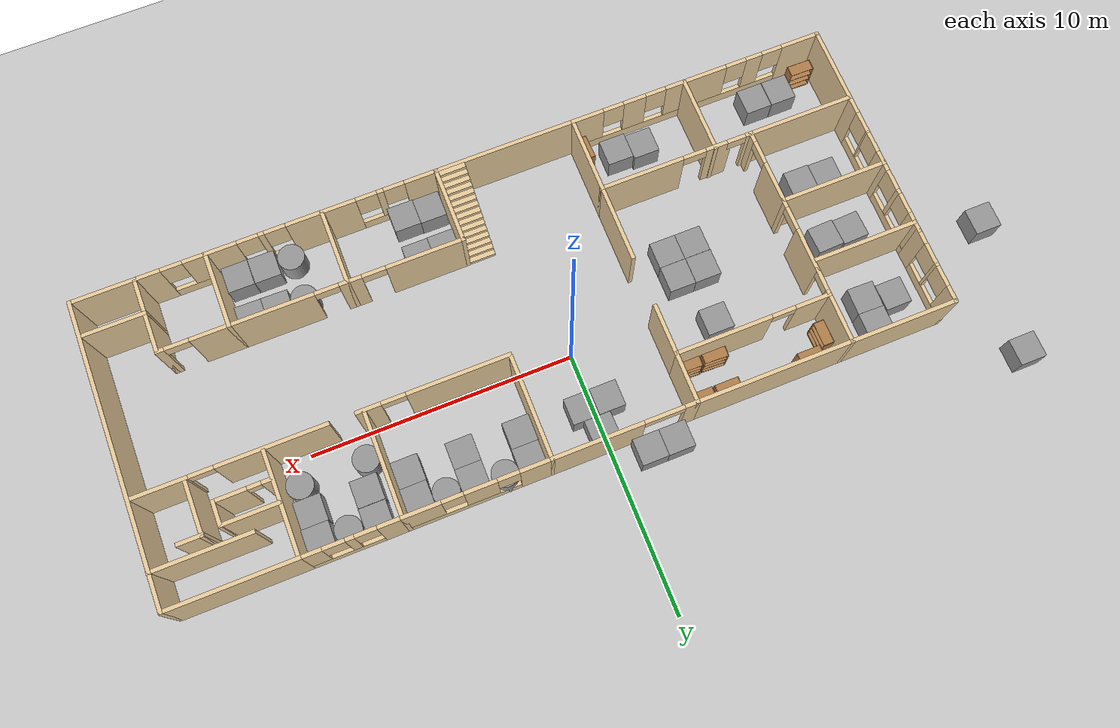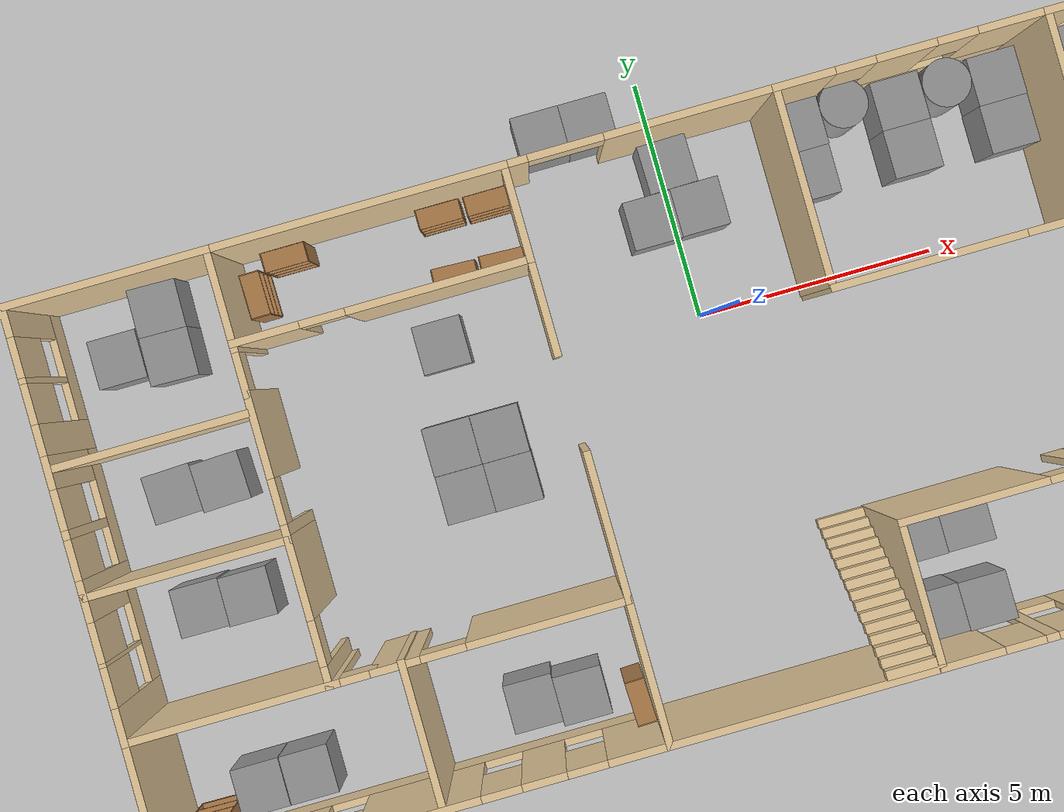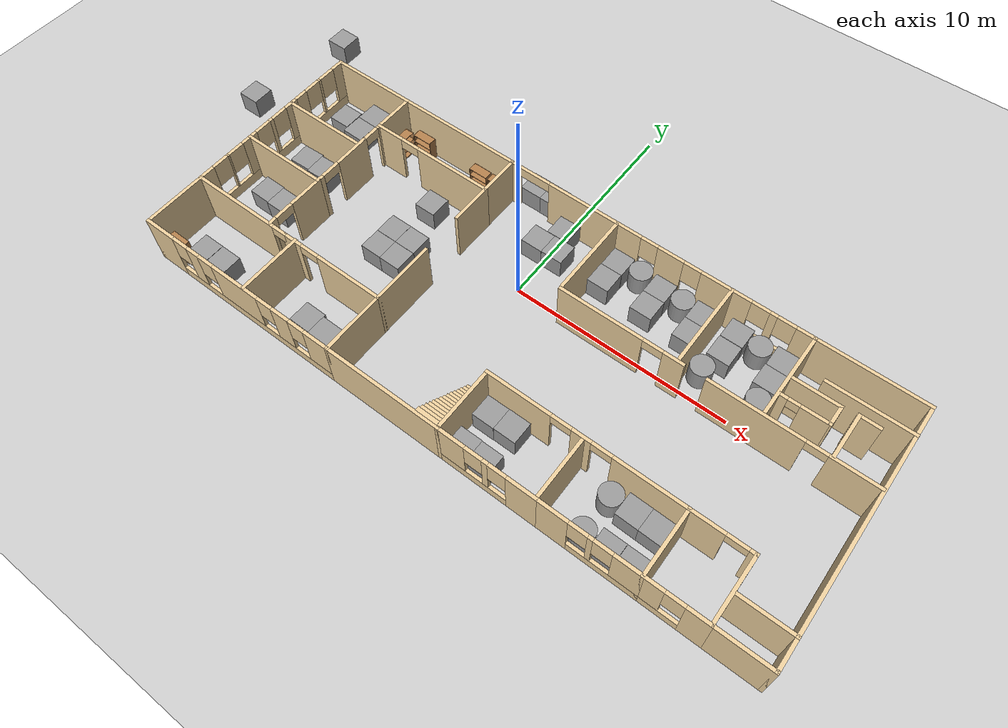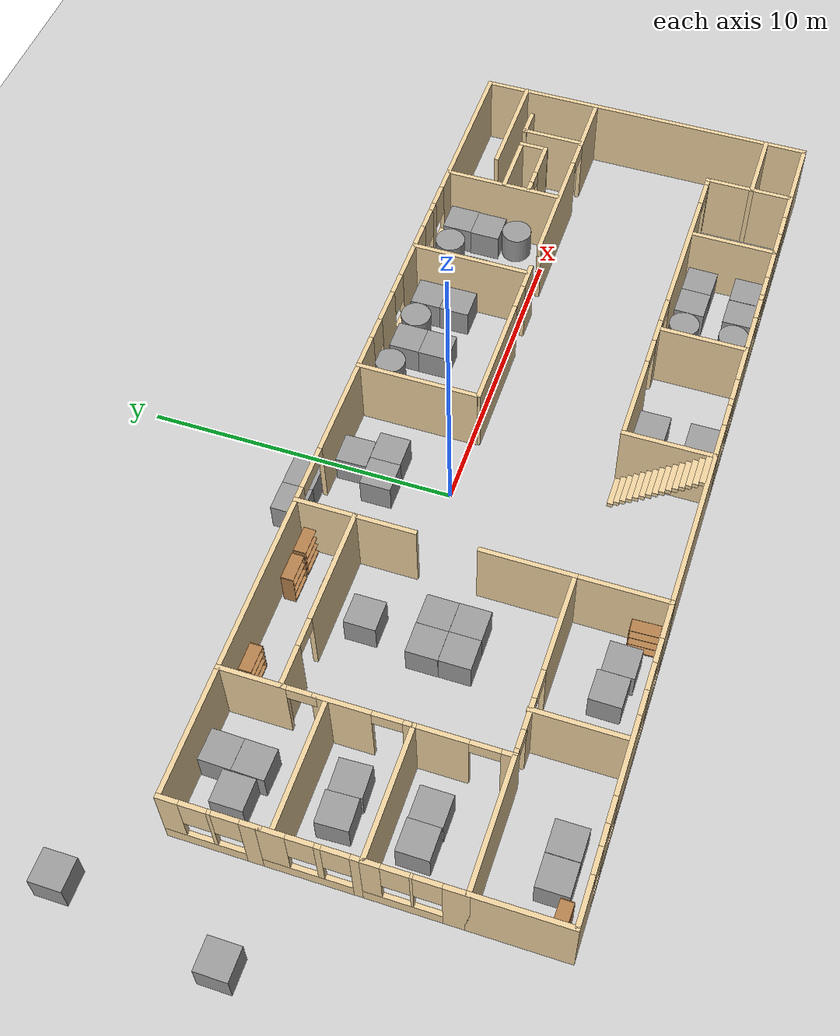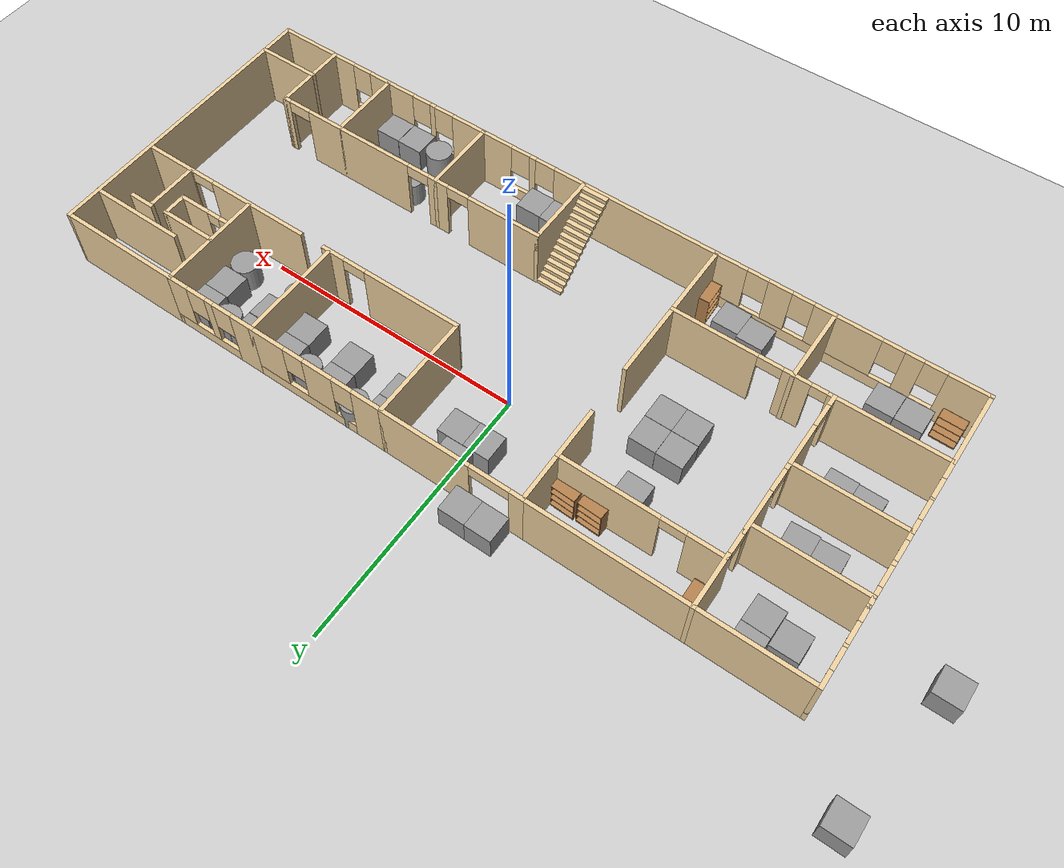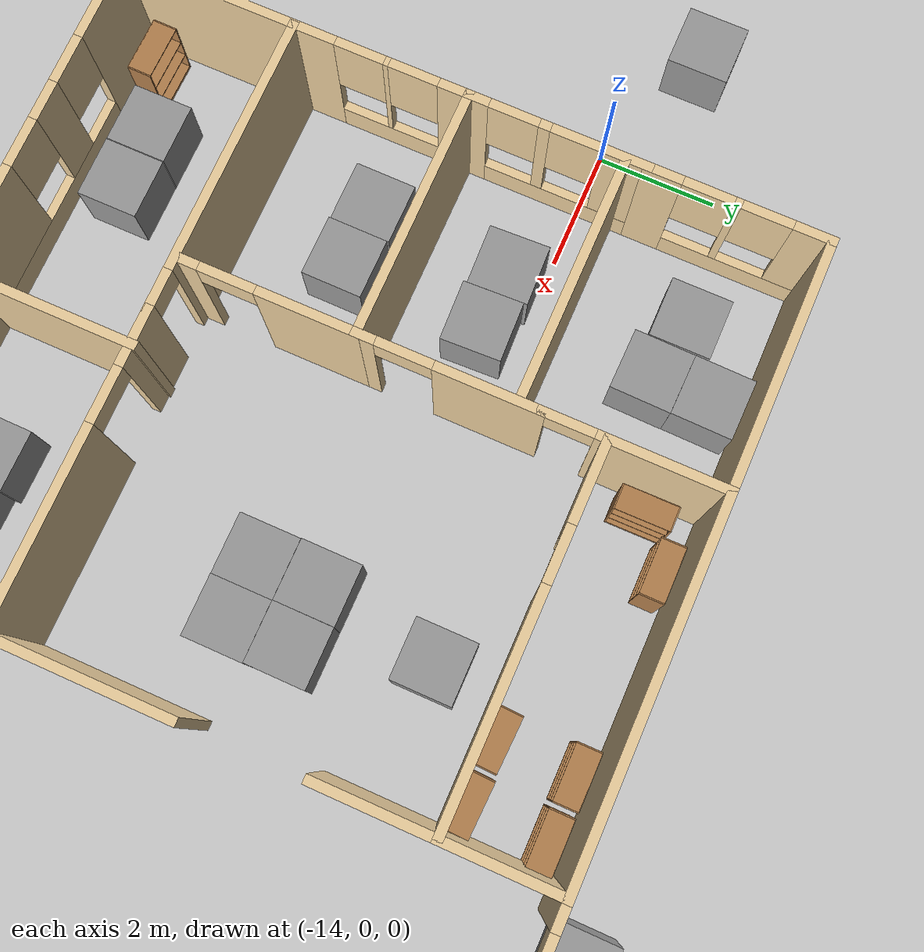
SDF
<sdf version="1.7">
 <world name="default">
  <light name="sun" type="directional">
   <pose>0 0 10 0 -0 0</pose>
   <diffuse>0.8 0.8 0.8 1</diffuse>
   <specular>0.2 0.2 0.2 1</specular>
   <attenuation>
    <range>1000</range>
    <constant>0.9</constant>
    <linear>0.01</linear>
    <quadratic>0.001</quadratic>
   </attenuation>
   <direction>-0.5 0.1 -0.9</direction>
   <spot><inner_angle>0</inner_angle><outer_angle>0</outer_angle><falloff>0</falloff></spot>
  </light>
  <model name="ground_plane">
   <static>1</static>
   <link name="link">
    <collision name="collision">
     <geometry><plane><normal>0 0 1</normal><size>100 100</size></plane></geometry>
     <surface>
      <contact><collide_bitmask>65535</collide_bitmask></contact>
      <friction><ode><mu>100</mu><mu2>50</mu2></ode></friction>
     </surface>
    </collision>
    <visual name="visual">
     <cast_shadows>0</cast_shadows>
     <geometry><plane><normal>0 0 1</normal><size>100 100</size></plane></geometry>
     <material>
      <script><uri>file://media/materials/scripts/gazebo.material</uri><name>Gazebo/Grey</name></script>
     </material>
    </visual>
   </link>
  </model>
  <gravity>0 0 -9.8</gravity>
  <magnetic_field>6e-06 2.3e-05 -4.2e-05</magnetic_field>
  <atmosphere type="adiabatic"/>
  <physics type="ode">
   <max_step_size>0.001</max_step_size>
   <real_time_factor>1</real_time_factor>
   <real_time_update_rate>1000</real_time_update_rate>
  </physics>
  <scene><ambient>0.4 0.4 0.4 1</ambient><background>0.7 0.7 0.7 1</background><shadows>1</shadows></scene>
  <audio><device>default</device></audio>
  <spherical_coordinates>
   <surface_model>EARTH_WGS84</surface_model>
   <latitude_deg>0</latitude_deg>
   <longitude_deg>0</longitude_deg>
   <elevation>0</elevation>
   <heading_deg>0</heading_deg>
  </spherical_coordinates>
  <model name="Health_2">
   <pose>1.45683 -1.97013 0 0 -0 0</pose>
   <link name="Stairs_1">
    <visual name="Stairs_1_Visual_0">
     <pose>0.20143 -2.88494 0.083333 0 -0 0</pose>
     <geometry><box><size>1 0.190191 0.166667</size></box></geometry>
     <material>
      <script><uri>file://media/materials/scripts/gazebo.material</uri><name>Gazebo/Grey</name></script>
      <ambient>0.921569 0.807843 0.615686 1</ambient>
     </material>
     <meta><layer>0</layer></meta>
    </visual>
    <collision name="Stairs_1_Collision_0">
     <geometry><box><size>1 0.190191 0.166667</size></box></geometry>
     <pose>0.20143 -2.88494 0.083333 0 -0 0</pose>
    </collision>
    <visual name="Stairs_1_Visual_1">
     <pose>0.20143 -3.07513 0.25 0 -0 0</pose>
     <geometry><box><size>1 0.190191 0.166667</size></box></geometry>
     <material>
      <script><uri>file://media/materials/scripts/gazebo.material</uri><name>Gazebo/Grey</name></script>
      <ambient>0.921569 0.807843 0.615686 1</ambient>
     </material>
     <meta><layer>0</layer></meta>
    </visual>
    <collision name="Stairs_1_Collision_1">
     <geometry><box><size>1 0.190191 0.166667</size></box></geometry>
     <pose>0.20143 -3.07513 0.25 0 -0 0</pose>
    </collision>
    <visual name="Stairs_1_Visual_2">
     <pose>0.20143 -3.26532 0.416667 0 -0 0</pose>
     <geometry><box><size>1 0.190191 0.166667</size></box></geometry>
     <material>
      <script><uri>file://media/materials/scripts/gazebo.material</uri><name>Gazebo/Grey</name></script>
      <ambient>0.921569 0.807843 0.615686 1</ambient>
     </material>
     <meta><layer>0</layer></meta>
    </visual>
    <collision name="Stairs_1_Collision_2">
     <geometry><box><size>1 0.190191 0.166667</size></box></geometry>
     <pose>0.20143 -3.26532 0.416667 0 -0 0</pose>
    </collision>
    <visual name="Stairs_1_Visual_3">
     <pose>0.20143 -3.45552 0.583333 0 -0 0</pose>
     <geometry><box><size>1 0.190191 0.166667</size></box></geometry>
     <material>
      <script><uri>file://media/materials/scripts/gazebo.material</uri><name>Gazebo/Grey</name></script>
      <ambient>0.921569 0.807843 0.615686 1</ambient>
     </material>
     <meta><layer>0</layer></meta>
    </visual>
    <collision name="Stairs_1_Collision_3">
     <geometry><box><size>1 0.190191 0.166667</size></box></geometry>
     <pose>0.20143 -3.45552 0.583333 0 -0 0</pose>
    </collision>
    <visual name="Stairs_1_Visual_4">
     <pose>0.20143 -3.64571 0.75 0 -0 0</pose>
     <geometry><box><size>1 0.190191 0.166667</size></box></geometry>
     <material>
      <script><uri>file://media/materials/scripts/gazebo.material</uri><name>Gazebo/Grey</name></script>
      <ambient>0.921569 0.807843 0.615686 1</ambient>
     </material>
     <meta><layer>0</layer></meta>
    </visual>
    <collision name="Stairs_1_Collision_4">
     <geometry><box><size>1 0.190191 0.166667</size></box></geometry>
     <pose>0.20143 -3.64571 0.75 0 -0 0</pose>
    </collision>
    <visual name="Stairs_1_Visual_5">
     <pose>0.20143 -3.8359 0.916667 0 -0 0</pose>
     <geometry><box><size>1 0.190191 0.166667</size></box></geometry>
     <material>
      <script><uri>file://media/materials/scripts/gazebo.material</uri><name>Gazebo/Grey</name></script>
      <ambient>0.921569 0.807843 0.615686 1</ambient>
     </material>
     <meta><layer>0</layer></meta>
    </visual>
    <collision name="Stairs_1_Collision_5">
     <geometry><box><size>1 0.190191 0.166667</size></box></geometry>
     <pose>0.20143 -3.8359 0.916667 0 -0 0</pose>
    </collision>
    <visual name="Stairs_1_Visual_6">
     <pose>0.20143 -4.02609 1.08333 0 -0 0</pose>
     <geometry><box><size>1 0.190191 0.166667</size></box></geometry>
     <material>
      <script><uri>file://media/materials/scripts/gazebo.material</uri><name>Gazebo/Grey</name></script>
      <ambient>0.921569 0.807843 0.615686 1</ambient>
     </material>
     <meta><layer>0</layer></meta>
    </visual>
    <collision name="Stairs_1_Collision_6">
     <geometry><box><size>1 0.190191 0.166667</size></box></geometry>
     <pose>0.20143 -4.02609 1.08333 0 -0 0</pose>
    </collision>
    <visual name="Stairs_1_Visual_7">
     <pose>0.20143 -4.21628 1.25 0 -0 0</pose>
     <geometry><box><size>1 0.190191 0.166667</size></box></geometry>
     <material>
      <script><uri>file://media/materials/scripts/gazebo.material</uri><name>Gazebo/Grey</name></script>
      <ambient>0.921569 0.807843 0.615686 1</ambient>
     </material>
     <meta><layer>0</layer></meta>
    </visual>
    <collision name="Stairs_1_Collision_7">
     <geometry><box><size>1 0.190191 0.166667</size></box></geometry>
     <pose>0.20143 -4.21628 1.25 0 -0 0</pose>
    </collision>
    <visual name="Stairs_1_Visual_8">
     <pose>0.20143 -4.40647 1.41667 0 -0 0</pose>
     <geometry><box><size>1 0.190191 0.166667</size></box></geometry>
     <material>
      <script><uri>file://media/materials/scripts/gazebo.material</uri><name>Gazebo/Grey</name></script>
      <ambient>0.921569 0.807843 0.615686 1</ambient>
     </material>
     <meta><layer>0</layer></meta>
    </visual>
    <collision name="Stairs_1_Collision_8">
     <geometry><box><size>1 0.190191 0.166667</size></box></geometry>
     <pose>0.20143 -4.40647 1.41667 0 -0 0</pose>
    </collision>
    <visual name="Stairs_1_Visual_9">
     <pose>0.20143 -4.59666 1.58333 0 -0 0</pose>
     <geometry><box><size>1 0.190191 0.166667</size></box></geometry>
     <material>
      <script><uri>file://media/materials/scripts/gazebo.material</uri><name>Gazebo/Grey</name></script>
      <ambient>0.921569 0.807843 0.615686 1</ambient>
     </material>
     <meta><layer>0</layer></meta>
    </visual>
    <collision name="Stairs_1_Collision_9">
     <geometry><box><size>1 0.190191 0.166667</size></box></geometry>
     <pose>0.20143 -4.59666 1.58333 0 -0 0</pose>
    </collision>
    <visual name="Stairs_1_Visual_10">
     <pose>0.20143 -4.78685 1.75 0 -0 0</pose>
     <geometry><box><size>1 0.190191 0.166667</size></box></geometry>
     <material>
      <script><uri>file://media/materials/scripts/gazebo.material</uri><name>Gazebo/Grey</name></script>
      <ambient>0.921569 0.807843 0.615686 1</ambient>
     </material>
     <meta><layer>0</layer></meta>
    </visual>
    <collision name="Stairs_1_Collision_10">
     <geometry><box><size>1 0.190191 0.166667</size></box></geometry>
     <pose>0.20143 -4.78685 1.75 0 -0 0</pose>
    </collision>
    <visual name="Stairs_1_Visual_11">
     <pose>0.20143 -4.97705 1.91667 0 -0 0</pose>
     <geometry><box><size>1 0.190191 0.166667</size></box></geometry>
     <material>
      <script><uri>file://media/materials/scripts/gazebo.material</uri><name>Gazebo/Grey</name></script>
      <ambient>0.921569 0.807843 0.615686 1</ambient>
     </material>
     <meta><layer>0</layer></meta>
    </visual>
    <collision name="Stairs_1_Collision_11">
     <geometry><box><size>1 0.190191 0.166667</size></box></geometry>
     <pose>0.20143 -4.97705 1.91667 0 -0 0</pose>
    </collision>
    <visual name="Stairs_1_Visual_12">
     <pose>0.20143 -5.16724 2.08333 0 -0 0</pose>
     <geometry><box><size>1 0.190191 0.166667</size></box></geometry>
     <material>
      <script><uri>file://media/materials/scripts/gazebo.material</uri><name>Gazebo/Grey</name></script>
      <ambient>0.921569 0.807843 0.615686 1</ambient>
     </material>
     <meta><layer>0</layer></meta>
    </visual>
    <collision name="Stairs_1_Collision_12">
     <geometry><box><size>1 0.190191 0.166667</size></box></geometry>
     <pose>0.20143 -5.16724 2.08333 0 -0 0</pose>
    </collision>
    <visual name="Stairs_1_Visual_13">
     <pose>0.20143 -5.35743 2.25 0 -0 0</pose>
     <geometry><box><size>1 0.190191 0.166667</size></box></geometry>
     <material>
      <script><uri>file://media/materials/scripts/gazebo.material</uri><name>Gazebo/Grey</name></script>
      <ambient>0.921569 0.807843 0.615686 1</ambient>
     </material>
     <meta><layer>0</layer></meta>
    </visual>
    <collision name="Stairs_1_Collision_13">
     <geometry><box><size>1 0.190191 0.166667</size></box></geometry>
     <pose>0.20143 -5.35743 2.25 0 -0 0</pose>
    </collision>
    <visual name="Stairs_1_Visual_14">
     <pose>0.20143 -5.54762 2.41667 0 -0 0</pose>
     <geometry><box><size>1 0.190191 0.166667</size></box></geometry>
     <material>
      <script><uri>file://media/materials/scripts/gazebo.material</uri><name>Gazebo/Grey</name></script>
      <ambient>0.921569 0.807843 0.615686 1</ambient>
     </material>
     <meta><layer>0</layer></meta>
    </visual>
    <collision name="Stairs_1_Collision_14">
     <geometry><box><size>1 0.190191 0.166667</size></box></geometry>
     <pose>0.20143 -5.54762 2.41667 0 -0 0</pose>
    </collision>
   </link>
   <link name="Wall_101">
    <pose>-10.4424 1.425 0 0 -0 -1.5708</pose>
    <visual name="Wall_101_Visual_0">
     <pose>-0.635885 0 1.25 0 -0 0</pose>
     <geometry><box><size>1.72823 0.15 2.5</size></box></geometry>
     <material>
      <script><uri>file://media/materials/scripts/gazebo.material</uri><name>Gazebo/Grey</name></script>
      <ambient>0.921569 0.807843 0.615686 1</ambient>
     </material>
     <meta><layer>0</layer></meta>
    </visual>
    <collision name="Wall_101_Collision_0">
     <geometry><box><size>1.72823 0.15 2.5</size></box></geometry>
     <pose>-0.635885 0 1.25 0 -0 0</pose>
    </collision>
    <visual name="Wall_101_Visual_1">
     <pose>1.31411 0 1.25 0 -0 0</pose>
     <geometry><box><size>0.371769 0.15 2.5</size></box></geometry>
     <material>
      <script><uri>file://media/materials/scripts/gazebo.material</uri><name>Gazebo/Grey</name></script>
      <ambient>0.921569 0.807843 0.615686 1</ambient>
     </material>
     <meta><layer>0</layer></meta>
    </visual>
    <collision name="Wall_101_Collision_1">
     <geometry><box><size>0.371769 0.15 2.5</size></box></geometry>
     <pose>1.31411 0 1.25 0 -0 0</pose>
    </collision>
    <visual name="Wall_101_Visual_2">
     <pose>0.678231 0 2.25 0 -0 0</pose>
     <geometry><box><size>0.9 0.15 0.5</size></box></geometry>
     <material>
      <script><uri>file://media/materials/scripts/gazebo.material</uri><name>Gazebo/Grey</name></script>
      <ambient>0.921569 0.807843 0.615686 1</ambient>
     </material>
     <meta><layer>0</layer></meta>
    </visual>
    <collision name="Wall_101_Collision_2">
     <geometry><box><size>0.9 0.15 0.5</size></box></geometry>
     <pose>0.678231 0 2.25 0 -0 0</pose>
    </collision>
   </link>
   <link name="Wall_103">
    <pose>-14.4424 4.275 0 0 -0 1.5708</pose>
    <visual name="Wall_103_Visual_0">
     <pose>-1.1898 0 1.25 0 -0 0</pose>
     <geometry><box><size>0.620394 0.15 2.5</size></box></geometry>
     <material>
      <script><uri>file://media/materials/scripts/gazebo.material</uri><name>Gazebo/Grey</name></script>
      <ambient>0.921569 0.807843 0.615686 1</ambient>
     </material>
     <meta><layer>0</layer></meta>
    </visual>
    <collision name="Wall_103_Collision_0">
     <geometry><box><size>0.620394 0.15 2.5</size></box></geometry>
     <pose>-1.1898 0 1.25 0 -0 0</pose>
    </collision>
    <visual name="Wall_103_Visual_1">
     <pose>0.310197 0 0.25 0 -0 0</pose>
     <geometry><box><size>2.37961 0.15 0.5</size></box></geometry>
     <material>
      <script><uri>file://media/materials/scripts/gazebo.material</uri><name>Gazebo/Grey</name></script>
      <ambient>0.921569 0.807843 0.615686 1</ambient>
     </material>
     <meta><layer>0</layer></meta>
    </visual>
    <collision name="Wall_103_Collision_1">
     <geometry><box><size>2.37961 0.15 0.5</size></box></geometry>
     <pose>0.310197 0 0.25 0 -0 0</pose>
    </collision>
    <visual name="Wall_103_Visual_2">
     <pose>-0.022282 0 1.5 0 -0 0</pose>
     <geometry><box><size>0.114648 0.15 2</size></box></geometry>
     <material>
      <script><uri>file://media/materials/scripts/gazebo.material</uri><name>Gazebo/Grey</name></script>
      <ambient>0.921569 0.807843 0.615686 1</ambient>
     </material>
     <meta><layer>0</layer></meta>
    </visual>
    <collision name="Wall_103_Collision_2">
     <geometry><box><size>0.114648 0.15 2</size></box></geometry>
     <pose>-0.022282 0 1.5 0 -0 0</pose>
    </collision>
    <visual name="Wall_103_Visual_3">
     <pose>1.16752 0 1.5 0 -0 0</pose>
     <geometry><box><size>0.664958 0.15 2</size></box></geometry>
     <material>
      <script><uri>file://media/materials/scripts/gazebo.material</uri><name>Gazebo/Grey</name></script>
      <ambient>0.921569 0.807843 0.615686 1</ambient>
     </material>
     <meta><layer>0</layer></meta>
    </visual>
    <collision name="Wall_103_Collision_3">
     <geometry><box><size>0.664958 0.15 2</size></box></geometry>
     <pose>1.16752 0 1.5 0 -0 0</pose>
    </collision>
    <visual name="Wall_103_Visual_4">
     <pose>-0.479606 0 1.9 0 -0 0</pose>
     <geometry><box><size>0.8 0.15 1.2</size></box></geometry>
     <material>
      <script><uri>file://media/materials/scripts/gazebo.material</uri><name>Gazebo/Grey</name></script>
      <ambient>0.921569 0.807843 0.615686 1</ambient>
     </material>
     <meta><layer>0</layer></meta>
    </visual>
    <collision name="Wall_103_Collision_4">
     <geometry><box><size>0.8 0.15 1.2</size></box></geometry>
     <pose>-0.479606 0 1.9 0 -0 0</pose>
    </collision>
    <visual name="Wall_103_Visual_5">
     <pose>0.435042 0 1.9 0 -0 0</pose>
     <geometry><box><size>0.8 0.15 1.2</size></box></geometry>
     <material>
      <script><uri>file://media/materials/scripts/gazebo.material</uri><name>Gazebo/Grey</name></script>
      <ambient>0.921569 0.807843 0.615686 1</ambient>
     </material>
     <meta><layer>0</layer></meta>
    </visual>
    <collision name="Wall_103_Collision_5">
     <geometry><box><size>0.8 0.15 1.2</size></box></geometry>
     <pose>0.435042 0 1.9 0 -0 0</pose>
    </collision>
   </link>
   <link name="Wall_104">
    <collision name="Wall_104_Collision">
     <geometry><box><size>4.15 0.15 2.5</size></box></geometry>
     <pose>0 0 1.25 0 -0 0</pose>
    </collision>
    <visual name="Wall_104_Visual">
     <pose>0 0 1.25 0 -0 0</pose>
     <geometry><box><size>4.15 0.15 2.5</size></box></geometry>
     <material>
      <script><uri>file://media/materials/scripts/gazebo.material</uri><name>Gazebo/Grey</name></script>
      <ambient>0.921569 0.807843 0.615686 1</ambient>
     </material>
     <meta><layer>0</layer></meta>
    </visual>
    <pose>-12.4424 5.7 0 0 -0 0</pose>
   </link>
   <link name="Wall_105">
    <pose>-10.4424 4.275 0 0 -0 -1.5708</pose>
    <visual name="Wall_105_Visual_0">
     <pose>-0.448372 0 1.25 0 -0 0</pose>
     <geometry><box><size>2.10326 0.15 2.5</size></box></geometry>
     <material>
      <script><uri>file://media/materials/scripts/gazebo.material</uri><name>Gazebo/Grey</name></script>
      <ambient>0.921569 0.807843 0.615686 1</ambient>
     </material>
     <meta><layer>0</layer></meta>
    </visual>
    <collision name="Wall_105_Collision_0">
     <geometry><box><size>2.10326 0.15 2.5</size></box></geometry>
     <pose>-0.448372 0 1.25 0 -0 0</pose>
    </collision>
    <visual name="Wall_105_Visual_1">
     <pose>1.05163 0 2.25 0 -0 0</pose>
     <geometry><box><size>0.896744 0.15 0.5</size></box></geometry>
     <material>
      <script><uri>file://media/materials/scripts/gazebo.material</uri><name>Gazebo/Grey</name></script>
      <ambient>0.921569 0.807843 0.615686 1</ambient>
     </material>
     <meta><layer>0</layer></meta>
    </visual>
    <collision name="Wall_105_Collision_1">
     <geometry><box><size>0.896744 0.15 0.5</size></box></geometry>
     <pose>1.05163 0 2.25 0 -0 0</pose>
    </collision>
   </link>
   <link name="Wall_107">
    <collision name="Wall_107_Collision">
     <geometry><box><size>6 0.15 2.5</size></box></geometry>
     <pose>0 0 1.25 0 -0 0</pose>
    </collision>
    <visual name="Wall_107_Visual">
     <pose>0 0 1.25 0 -0 0</pose>
     <geometry><box><size>6 0.15 2.5</size></box></geometry>
     <material>
      <script><uri>file://media/materials/scripts/gazebo.material</uri><name>Gazebo/Grey</name></script>
      <ambient>0.921569 0.807843 0.615686 1</ambient>
     </material>
     <meta><layer>0</layer></meta>
    </visual>
    <pose>-7.51736 5.7 0 0 -0 0</pose>
   </link>
   <link name="Wall_114">
    <pose>-10.4424 -1.425 0 0 -0 -1.5708</pose>
    <visual name="Wall_114_Visual_0">
     <pose>-0.673048 0 1.25 0 -0 0</pose>
     <geometry><box><size>1.6539 0.15 2.5</size></box></geometry>
     <material>
      <script><uri>file://media/materials/scripts/gazebo.material</uri><name>Gazebo/Grey</name></script>
      <ambient>0.921569 0.807843 0.615686 1</ambient>
     </material>
     <meta><layer>0</layer></meta>
    </visual>
    <collision name="Wall_114_Collision_0">
     <geometry><box><size>1.6539 0.15 2.5</size></box></geometry>
     <pose>-0.673048 0 1.25 0 -0 0</pose>
    </collision>
    <visual name="Wall_114_Visual_1">
     <pose>1.27695 0 1.25 0 -0 0</pose>
     <geometry><box><size>0.446096 0.15 2.5</size></box></geometry>
     <material>
      <script><uri>file://media/materials/scripts/gazebo.material</uri><name>Gazebo/Grey</name></script>
      <ambient>0.921569 0.807843 0.615686 1</ambient>
     </material>
     <meta><layer>0</layer></meta>
    </visual>
    <collision name="Wall_114_Collision_1">
     <geometry><box><size>0.446096 0.15 2.5</size></box></geometry>
     <pose>1.27695 0 1.25 0 -0 0</pose>
    </collision>
    <visual name="Wall_114_Visual_2">
     <pose>0.603904 0 2.25 0 -0 0</pose>
     <geometry><box><size>0.9 0.15 0.5</size></box></geometry>
     <material>
      <script><uri>file://media/materials/scripts/gazebo.material</uri><name>Gazebo/Grey</name></script>
      <ambient>0.921569 0.807843 0.615686 1</ambient>
     </material>
     <meta><layer>0</layer></meta>
    </visual>
    <collision name="Wall_114_Collision_2">
     <geometry><box><size>0.9 0.15 0.5</size></box></geometry>
     <pose>0.603904 0 2.25 0 -0 0</pose>
    </collision>
   </link>
   <link name="Wall_122">
    <collision name="Wall_122_Collision">
     <geometry><box><size>2 0.15 2.5</size></box></geometry>
     <pose>0 0 1.25 0 -0 0</pose>
    </collision>
    <visual name="Wall_122_Visual">
     <pose>0 0 1.25 0 -0 0</pose>
     <geometry><box><size>2 0.15 2.5</size></box></geometry>
     <material>
      <script><uri>file://media/materials/scripts/gazebo.material</uri><name>Gazebo/Grey</name></script>
      <ambient>0.921569 0.807843 0.615686 1</ambient>
     </material>
     <meta><layer>0</layer></meta>
    </visual>
    <pose>-4.59236 4.775 0 0 -0 -1.5708</pose>
   </link>
   <link name="Wall_123">
    <pose>-7.51736 3.85 0 0 -0 3.14159</pose>
    <visual name="Wall_123_Visual_0">
     <pose>-1.14066 0 1.25 0 -0 0</pose>
     <geometry><box><size>3.71867 0.15 2.5</size></box></geometry>
     <material>
      <script><uri>file://media/materials/scripts/gazebo.material</uri><name>Gazebo/Grey</name></script>
      <ambient>0.921569 0.807843 0.615686 1</ambient>
     </material>
     <meta><layer>0</layer></meta>
    </visual>
    <collision name="Wall_123_Collision_0">
     <geometry><box><size>3.71867 0.15 2.5</size></box></geometry>
     <pose>-1.14066 0 1.25 0 -0 0</pose>
    </collision>
    <visual name="Wall_123_Visual_1">
     <pose>2.30934 0 1.25 0 -0 0</pose>
     <geometry><box><size>1.38133 0.15 2.5</size></box></geometry>
     <material>
      <script><uri>file://media/materials/scripts/gazebo.material</uri><name>Gazebo/Grey</name></script>
      <ambient>0.921569 0.807843 0.615686 1</ambient>
     </material>
     <meta><layer>0</layer></meta>
    </visual>
    <collision name="Wall_123_Collision_1">
     <geometry><box><size>1.38133 0.15 2.5</size></box></geometry>
     <pose>2.30934 0 1.25 0 -0 0</pose>
    </collision>
    <visual name="Wall_123_Visual_2">
     <pose>1.16867 0 2.25 0 -0 0</pose>
     <geometry><box><size>0.9 0.15 0.5</size></box></geometry>
     <material>
      <script><uri>file://media/materials/scripts/gazebo.material</uri><name>Gazebo/Grey</name></script>
      <ambient>0.921569 0.807843 0.615686 1</ambient>
     </material>
     <meta><layer>0</layer></meta>
    </visual>
    <collision name="Wall_123_Collision_2">
     <geometry><box><size>0.9 0.15 0.5</size></box></geometry>
     <pose>1.16867 0 2.25 0 -0 0</pose>
    </collision>
   </link>
   <link name="Wall_125">
    <collision name="Wall_125_Collision">
     <geometry><box><size>2 0.15 2.5</size></box></geometry>
     <pose>0 0 1.25 0 -0 0</pose>
    </collision>
    <visual name="Wall_125_Visual">
     <pose>0 0 1.25 0 -0 0</pose>
     <geometry><box><size>2 0.15 2.5</size></box></geometry>
     <material>
      <script><uri>file://media/materials/scripts/gazebo.material</uri><name>Gazebo/Grey</name></script>
      <ambient>0.921569 0.807843 0.615686 1</ambient>
     </material>
     <meta><layer>0</layer></meta>
    </visual>
    <pose>-4.59236 2.925 0 0 -0 -1.5708</pose>
   </link>
   <link name="Wall_127">
    <collision name="Wall_127_Collision">
     <geometry><box><size>3 0.15 2.5</size></box></geometry>
     <pose>0 0 1.25 0 -0 0</pose>
    </collision>
    <visual name="Wall_127_Visual">
     <pose>0 0 1.25 0 -0 0</pose>
     <geometry><box><size>3 0.15 2.5</size></box></geometry>
     <material>
      <script><uri>file://media/materials/scripts/gazebo.material</uri><name>Gazebo/Grey</name></script>
      <ambient>0.921569 0.807843 0.615686 1</ambient>
     </material>
     <meta><layer>0</layer></meta>
    </visual>
    <pose>-4.56923 -1.425 0 0 -0 1.5708</pose>
   </link>
   <link name="Wall_133">
    <collision name="Wall_133_Collision">
     <geometry><box><size>3 0.15 2.5</size></box></geometry>
     <pose>0 0 1.25 0 -0 0</pose>
    </collision>
    <visual name="Wall_133_Visual">
     <pose>0 0 1.25 0 -0 0</pose>
     <geometry><box><size>3 0.15 2.5</size></box></geometry>
     <material>
      <script><uri>file://media/materials/scripts/gazebo.material</uri><name>Gazebo/Grey</name></script>
      <ambient>0.921569 0.807843 0.615686 1</ambient>
     </material>
     <meta><layer>0</layer></meta>
    </visual>
    <pose>-14.4424 -4.275 0 0 -0 -1.5708</pose>
   </link>
   <link name="Wall_134">
    <pose>-9.5058 -5.7 0 0 -0 0</pose>
    <visual name="Wall_134_Visual_0">
     <pose>-4.24101 0 1.25 0 -0 0</pose>
     <geometry><box><size>1.54111 0.15 2.5</size></box></geometry>
     <material>
      <script><uri>file://media/materials/scripts/gazebo.material</uri><name>Gazebo/Grey</name></script>
      <ambient>0.921569 0.807843 0.615686 1</ambient>
     </material>
     <meta><layer>0</layer></meta>
    </visual>
    <collision name="Wall_134_Collision_0">
     <geometry><box><size>1.54111 0.15 2.5</size></box></geometry>
     <pose>-4.24101 0 1.25 0 -0 0</pose>
    </collision>
    <visual name="Wall_134_Visual_1">
     <pose>0.770556 0 0.25 0 -0 0</pose>
     <geometry><box><size>8.48202 0.15 0.5</size></box></geometry>
     <material>
      <script><uri>file://media/materials/scripts/gazebo.material</uri><name>Gazebo/Grey</name></script>
      <ambient>0.921569 0.807843 0.615686 1</ambient>
     </material>
     <meta><layer>0</layer></meta>
    </visual>
    <collision name="Wall_134_Collision_1">
     <geometry><box><size>8.48202 0.15 0.5</size></box></geometry>
     <pose>0.770556 0 0.25 0 -0 0</pose>
    </collision>
    <visual name="Wall_134_Visual_2">
     <pose>-2.34288 0 1.5 0 -0 0</pose>
     <geometry><box><size>0.655137 0.15 2</size></box></geometry>
     <material>
      <script><uri>file://media/materials/scripts/gazebo.material</uri><name>Gazebo/Grey</name></script>
      <ambient>0.921569 0.807843 0.615686 1</ambient>
     </material>
     <meta><layer>0</layer></meta>
    </visual>
    <collision name="Wall_134_Collision_2">
     <geometry><box><size>0.655137 0.15 2</size></box></geometry>
     <pose>-2.34288 0 1.5 0 -0 0</pose>
    </collision>
    <visual name="Wall_134_Visual_3">
     <pose>0.011093 0 1.5 0 -0 0</pose>
     <geometry><box><size>2.45282 0.15 2</size></box></geometry>
     <material>
      <script><uri>file://media/materials/scripts/gazebo.material</uri><name>Gazebo/Grey</name></script>
      <ambient>0.921569 0.807843 0.615686 1</ambient>
     </material>
     <meta><layer>0</layer></meta>
    </visual>
    <collision name="Wall_134_Collision_3">
     <geometry><box><size>2.45282 0.15 2</size></box></geometry>
     <pose>0.011093 0 1.5 0 -0 0</pose>
    </collision>
    <visual name="Wall_134_Visual_4">
     <pose>2.48179 0 1.5 0 -0 0</pose>
     <geometry><box><size>0.888581 0.15 2</size></box></geometry>
     <material>
      <script><uri>file://media/materials/scripts/gazebo.material</uri><name>Gazebo/Grey</name></script>
      <ambient>0.921569 0.807843 0.615686 1</ambient>
     </material>
     <meta><layer>0</layer></meta>
    </visual>
    <collision name="Wall_134_Collision_4">
     <geometry><box><size>0.888581 0.15 2</size></box></geometry>
     <pose>2.48179 0 1.5 0 -0 0</pose>
    </collision>
    <visual name="Wall_134_Visual_5">
     <pose>4.36882 0 1.5 0 -0 0</pose>
     <geometry><box><size>1.28548 0.15 2</size></box></geometry>
     <material>
      <script><uri>file://media/materials/scripts/gazebo.material</uri><name>Gazebo/Grey</name></script>
      <ambient>0.921569 0.807843 0.615686 1</ambient>
     </material>
     <meta><layer>0</layer></meta>
    </visual>
    <collision name="Wall_134_Collision_5">
     <geometry><box><size>1.28548 0.15 2</size></box></geometry>
     <pose>4.36882 0 1.5 0 -0 0</pose>
    </collision>
    <visual name="Wall_134_Visual_6">
     <pose>-3.07045 0 1.9 0 -0 0</pose>
     <geometry><box><size>0.8 0.15 1.2</size></box></geometry>
     <material>
      <script><uri>file://media/materials/scripts/gazebo.material</uri><name>Gazebo/Grey</name></script>
      <ambient>0.921569 0.807843 0.615686 1</ambient>
     </material>
     <meta><layer>0</layer></meta>
    </visual>
    <collision name="Wall_134_Collision_6">
     <geometry><box><size>0.8 0.15 1.2</size></box></geometry>
     <pose>-3.07045 0 1.9 0 -0 0</pose>
    </collision>
    <visual name="Wall_134_Visual_7">
     <pose>-1.61532 0 1.9 0 -0 0</pose>
     <geometry><box><size>0.8 0.15 1.2</size></box></geometry>
     <material>
      <script><uri>file://media/materials/scripts/gazebo.material</uri><name>Gazebo/Grey</name></script>
      <ambient>0.921569 0.807843 0.615686 1</ambient>
     </material>
     <meta><layer>0</layer></meta>
    </visual>
    <collision name="Wall_134_Collision_7">
     <geometry><box><size>0.8 0.15 1.2</size></box></geometry>
     <pose>-1.61532 0 1.9 0 -0 0</pose>
    </collision>
    <visual name="Wall_134_Visual_8">
     <pose>1.6375 0 1.9 0 -0 0</pose>
     <geometry><box><size>0.8 0.15 1.2</size></box></geometry>
     <material>
      <script><uri>file://media/materials/scripts/gazebo.material</uri><name>Gazebo/Grey</name></script>
      <ambient>0.921569 0.807843 0.615686 1</ambient>
     </material>
     <meta><layer>0</layer></meta>
    </visual>
    <collision name="Wall_134_Collision_8">
     <geometry><box><size>0.8 0.15 1.2</size></box></geometry>
     <pose>1.6375 0 1.9 0 -0 0</pose>
    </collision>
    <visual name="Wall_134_Visual_9">
     <pose>3.32608 0 1.9 0 -0 0</pose>
     <geometry><box><size>0.8 0.15 1.2</size></box></geometry>
     <material>
      <script><uri>file://media/materials/scripts/gazebo.material</uri><name>Gazebo/Grey</name></script>
      <ambient>0.921569 0.807843 0.615686 1</ambient>
     </material>
     <meta><layer>0</layer></meta>
    </visual>
    <collision name="Wall_134_Collision_9">
     <geometry><box><size>0.8 0.15 1.2</size></box></geometry>
     <pose>3.32608 0 1.9 0 -0 0</pose>
    </collision>
   </link>
   <link name="Wall_138">
    <pose>-1.91736 5.7 0 0 -0 0</pose>
    <visual name="Wall_138_Visual_0">
     <pose>-2.48035 0 1.25 0 -0 0</pose>
     <geometry><box><size>0.539308 0.15 2.5</size></box></geometry>
     <material>
      <script><uri>file://media/materials/scripts/gazebo.material</uri><name>Gazebo/Grey</name></script>
      <ambient>0.921569 0.807843 0.615686 1</ambient>
     </material>
     <meta><layer>0</layer></meta>
    </visual>
    <collision name="Wall_138_Collision_0">
     <geometry><box><size>0.539308 0.15 2.5</size></box></geometry>
     <pose>-2.48035 0 1.25 0 -0 0</pose>
    </collision>
    <visual name="Wall_138_Visual_1">
     <pose>1.01965 0 1.25 0 -0 0</pose>
     <geometry><box><size>3.46069 0.15 2.5</size></box></geometry>
     <material>
      <script><uri>file://media/materials/scripts/gazebo.material</uri><name>Gazebo/Grey</name></script>
      <ambient>0.921569 0.807843 0.615686 1</ambient>
     </material>
     <meta><layer>0</layer></meta>
    </visual>
    <collision name="Wall_138_Collision_1">
     <geometry><box><size>3.46069 0.15 2.5</size></box></geometry>
     <pose>1.01965 0 1.25 0 -0 0</pose>
    </collision>
    <visual name="Wall_138_Visual_2">
     <pose>-1.46069 0 2.25 0 -0 0</pose>
     <geometry><box><size>1.5 0.15 0.5</size></box></geometry>
     <material>
      <script><uri>file://media/materials/scripts/gazebo.material</uri><name>Gazebo/Grey</name></script>
      <ambient>0.921569 0.807843 0.615686 1</ambient>
     </material>
     <meta><layer>0</layer></meta>
    </visual>
    <collision name="Wall_138_Collision_2">
     <geometry><box><size>1.5 0.15 0.5</size></box></geometry>
     <pose>-1.46069 0 2.25 0 -0 0</pose>
    </collision>
   </link>
   <link name="Wall_140">
    <collision name="Wall_140_Collision">
     <geometry><box><size>4 0.15 2.5</size></box></geometry>
     <pose>0 0 1.25 0 -0 0</pose>
    </collision>
    <visual name="Wall_140_Visual">
     <pose>0 0 1.25 0 -0 0</pose>
     <geometry><box><size>4 0.15 2.5</size></box></geometry>
     <material>
      <script><uri>file://media/materials/scripts/gazebo.material</uri><name>Gazebo/Grey</name></script>
      <ambient>0.921569 0.807843 0.615686 1</ambient>
     </material>
     <meta><layer>0</layer></meta>
    </visual>
    <pose>0.757639 3.775 0 0 -0 -1.5708</pose>
   </link>
   <link name="Wall_145">
    <collision name="Wall_145_Collision">
     <geometry><box><size>3 0.15 2.5</size></box></geometry>
     <pose>0 0 1.25 0 -0 0</pose>
    </collision>
    <visual name="Wall_145_Visual">
     <pose>0 0 1.25 0 -0 0</pose>
     <geometry><box><size>3 0.15 2.5</size></box></geometry>
     <material>
      <script><uri>file://media/materials/scripts/gazebo.material</uri><name>Gazebo/Grey</name></script>
      <ambient>0.921569 0.807843 0.615686 1</ambient>
     </material>
     <meta><layer>0</layer></meta>
    </visual>
    <pose>9.48077 -4.275 0 0 -0 -1.5708</pose>
   </link>
   <link name="Wall_164">
    <pose>3.43264 5.7 0 0 -0 0</pose>
    <visual name="Wall_164_Visual_0">
     <pose>-2.12455 0 1.25 0 -0 0</pose>
     <geometry><box><size>1.25091 0.15 2.5</size></box></geometry>
     <material>
      <script><uri>file://media/materials/scripts/gazebo.material</uri><name>Gazebo/Grey</name></script>
      <ambient>0.921569 0.807843 0.615686 1</ambient>
     </material>
     <meta><layer>0</layer></meta>
    </visual>
    <collision name="Wall_164_Collision_0">
     <geometry><box><size>1.25091 0.15 2.5</size></box></geometry>
     <pose>-2.12455 0 1.25 0 -0 0</pose>
    </collision>
    <visual name="Wall_164_Visual_1">
     <pose>0.625454 0 0.25 0 -0 0</pose>
     <geometry><box><size>4.24909 0.15 0.5</size></box></geometry>
     <material>
      <script><uri>file://media/materials/scripts/gazebo.material</uri><name>Gazebo/Grey</name></script>
      <ambient>0.921569 0.807843 0.615686 1</ambient>
     </material>
     <meta><layer>0</layer></meta>
    </visual>
    <collision name="Wall_164_Collision_1">
     <geometry><box><size>4.24909 0.15 0.5</size></box></geometry>
     <pose>0.625454 0 0.25 0 -0 0</pose>
    </collision>
    <visual name="Wall_164_Visual_2">
     <pose>-0.096496 0 1.5 0 -0 0</pose>
     <geometry><box><size>1.20519 0.15 2</size></box></geometry>
     <material>
      <script><uri>file://media/materials/scripts/gazebo.material</uri><name>Gazebo/Grey</name></script>
      <ambient>0.921569 0.807843 0.615686 1</ambient>
     </material>
     <meta><layer>0</layer></meta>
    </visual>
    <collision name="Wall_164_Collision_2">
     <geometry><box><size>1.20519 0.15 2</size></box></geometry>
     <pose>-0.096496 0 1.5 0 -0 0</pose>
    </collision>
    <visual name="Wall_164_Visual_3">
     <pose>2.02805 0 1.5 0 -0 0</pose>
     <geometry><box><size>1.4439 0.15 2</size></box></geometry>
     <material>
      <script><uri>file://media/materials/scripts/gazebo.material</uri><name>Gazebo/Grey</name></script>
      <ambient>0.921569 0.807843 0.615686 1</ambient>
     </material>
     <meta><layer>0</layer></meta>
    </visual>
    <collision name="Wall_164_Collision_3">
     <geometry><box><size>1.4439 0.15 2</size></box></geometry>
     <pose>2.02805 0 1.5 0 -0 0</pose>
    </collision>
    <visual name="Wall_164_Visual_4">
     <pose>-1.09909 0 1.9 0 -0 0</pose>
     <geometry><box><size>0.8 0.15 1.2</size></box></geometry>
     <material>
      <script><uri>file://media/materials/scripts/gazebo.material</uri><name>Gazebo/Grey</name></script>
      <ambient>0.921569 0.807843 0.615686 1</ambient>
     </material>
     <meta><layer>0</layer></meta>
    </visual>
    <collision name="Wall_164_Collision_4">
     <geometry><box><size>0.8 0.15 1.2</size></box></geometry>
     <pose>-1.09909 0 1.9 0 -0 0</pose>
    </collision>
    <visual name="Wall_164_Visual_5">
     <pose>0.906098 0 1.9 0 -0 0</pose>
     <geometry><box><size>0.8 0.15 1.2</size></box></geometry>
     <material>
      <script><uri>file://media/materials/scripts/gazebo.material</uri><name>Gazebo/Grey</name></script>
      <ambient>0.921569 0.807843 0.615686 1</ambient>
     </material>
     <meta><layer>0</layer></meta>
    </visual>
    <collision name="Wall_164_Collision_5">
     <geometry><box><size>0.8 0.15 1.2</size></box></geometry>
     <pose>0.906098 0 1.9 0 -0 0</pose>
    </collision>
   </link>
   <link name="Wall_165">
    <collision name="Wall_165_Collision">
     <geometry><box><size>4 0.15 2.5</size></box></geometry>
     <pose>0 0 1.25 0 -0 0</pose>
    </collision>
    <visual name="Wall_165_Visual">
     <pose>0 0 1.25 0 -0 0</pose>
     <geometry><box><size>4 0.15 2.5</size></box></geometry>
     <material>
      <script><uri>file://media/materials/scripts/gazebo.material</uri><name>Gazebo/Grey</name></script>
      <ambient>0.921569 0.807843 0.615686 1</ambient>
     </material>
     <meta><layer>0</layer></meta>
    </visual>
    <pose>6.10764 3.775 0 0 -0 -1.5708</pose>
   </link>
   <link name="Wall_190">
    <pose>7.90764 5.7 0 0 -0 0</pose>
    <visual name="Wall_190_Visual_0">
     <pose>-1.39167 0 1.25 0 -0 0</pose>
     <geometry><box><size>0.966652 0.15 2.5</size></box></geometry>
     <material>
      <script><uri>file://media/materials/scripts/gazebo.material</uri><name>Gazebo/Grey</name></script>
      <ambient>0.921569 0.807843 0.615686 1</ambient>
     </material>
     <meta><layer>0</layer></meta>
    </visual>
    <collision name="Wall_190_Collision_0">
     <geometry><box><size>0.966652 0.15 2.5</size></box></geometry>
     <pose>-1.39167 0 1.25 0 -0 0</pose>
    </collision>
    <visual name="Wall_190_Visual_1">
     <pose>0.483326 0 0.25 0 -0 0</pose>
     <geometry><box><size>2.78335 0.15 0.5</size></box></geometry>
     <material>
      <script><uri>file://media/materials/scripts/gazebo.material</uri><name>Gazebo/Grey</name></script>
      <ambient>0.921569 0.807843 0.615686 1</ambient>
     </material>
     <meta><layer>0</layer></meta>
    </visual>
    <collision name="Wall_190_Collision_1">
     <geometry><box><size>2.78335 0.15 0.5</size></box></geometry>
     <pose>0.483326 0 0.25 0 -0 0</pose>
    </collision>
    <visual name="Wall_190_Visual_2">
     <pose>0.054512 0 1.5 0 -0 0</pose>
     <geometry><box><size>0.32572 0.15 2</size></box></geometry>
     <material>
      <script><uri>file://media/materials/scripts/gazebo.material</uri><name>Gazebo/Grey</name></script>
      <ambient>0.921569 0.807843 0.615686 1</ambient>
     </material>
     <meta><layer>0</layer></meta>
    </visual>
    <collision name="Wall_190_Collision_2">
     <geometry><box><size>0.32572 0.15 2</size></box></geometry>
     <pose>0.054512 0 1.5 0 -0 0</pose>
    </collision>
    <visual name="Wall_190_Visual_3">
     <pose>1.44619 0 1.5 0 -0 0</pose>
     <geometry><box><size>0.857628 0.15 2</size></box></geometry>
     <material>
      <script><uri>file://media/materials/scripts/gazebo.material</uri><name>Gazebo/Grey</name></script>
      <ambient>0.921569 0.807843 0.615686 1</ambient>
     </material>
     <meta><layer>0</layer></meta>
    </visual>
    <collision name="Wall_190_Collision_3">
     <geometry><box><size>0.857628 0.15 2</size></box></geometry>
     <pose>1.44619 0 1.5 0 -0 0</pose>
    </collision>
    <visual name="Wall_190_Visual_4">
     <pose>-0.508348 0 1.9 0 -0 0</pose>
     <geometry><box><size>0.8 0.15 1.2</size></box></geometry>
     <material>
      <script><uri>file://media/materials/scripts/gazebo.material</uri><name>Gazebo/Grey</name></script>
      <ambient>0.921569 0.807843 0.615686 1</ambient>
     </material>
     <meta><layer>0</layer></meta>
    </visual>
    <collision name="Wall_190_Collision_4">
     <geometry><box><size>0.8 0.15 1.2</size></box></geometry>
     <pose>-0.508348 0 1.9 0 -0 0</pose>
    </collision>
    <visual name="Wall_190_Visual_5">
     <pose>0.617372 0 1.9 0 -0 0</pose>
     <geometry><box><size>0.8 0.15 1.2</size></box></geometry>
     <material>
      <script><uri>file://media/materials/scripts/gazebo.material</uri><name>Gazebo/Grey</name></script>
      <ambient>0.921569 0.807843 0.615686 1</ambient>
     </material>
     <meta><layer>0</layer></meta>
    </visual>
    <collision name="Wall_190_Collision_5">
     <geometry><box><size>0.8 0.15 1.2</size></box></geometry>
     <pose>0.617372 0 1.9 0 -0 0</pose>
    </collision>
   </link>
   <link name="Wall_191">
    <collision name="Wall_191_Collision">
     <geometry><box><size>4 0.15 2.5</size></box></geometry>
     <pose>0 0 1.25 0 -0 0</pose>
    </collision>
    <visual name="Wall_191_Visual">
     <pose>0 0 1.25 0 -0 0</pose>
     <geometry><box><size>4 0.15 2.5</size></box></geometry>
     <material>
      <script><uri>file://media/materials/scripts/gazebo.material</uri><name>Gazebo/Grey</name></script>
      <ambient>0.921569 0.807843 0.615686 1</ambient>
     </material>
     <meta><layer>0</layer></meta>
    </visual>
    <pose>9.70764 3.775 0 0 -0 -1.5708</pose>
   </link>
   <link name="Wall_203">
    <collision name="Wall_203_Collision">
     <geometry><box><size>11.55 0.15 2.5</size></box></geometry>
     <pose>0 0 1.25 0 -0 0</pose>
    </collision>
    <visual name="Wall_203_Visual">
     <pose>0 0 1.25 0 -0 0</pose>
     <geometry><box><size>11.55 0.15 2.5</size></box></geometry>
     <material>
      <script><uri>file://media/materials/scripts/gazebo.material</uri><name>Gazebo/Grey</name></script>
      <ambient>0.921569 0.807843 0.615686 1</ambient>
     </material>
     <meta><layer>0</layer></meta>
    </visual>
    <pose>14.4308 -0 0 0 -0 1.5708</pose>
   </link>
   <link name="Wall_206">
    <collision name="Wall_206_Collision">
     <geometry><box><size>4.87313 0.15 2.5</size></box></geometry>
     <pose>0 0 1.25 0 -0 0</pose>
    </collision>
    <visual name="Wall_206_Visual">
     <pose>0 0 1.25 0 -0 0</pose>
     <geometry><box><size>4.87313 0.15 2.5</size></box></geometry>
     <material>
      <script><uri>file://media/materials/scripts/gazebo.material</uri><name>Gazebo/Grey</name></script>
      <ambient>0.921569 0.807843 0.615686 1</ambient>
     </material>
     <meta><layer>0</layer></meta>
    </visual>
    <pose>12.0692 5.7 0 0 -0 0</pose>
   </link>
   <link name="Wall_222">
    <collision name="Wall_222_Collision">
     <geometry><box><size>2.5 0.15 2.5</size></box></geometry>
     <pose>0 0 1.25 0 -0 0</pose>
    </collision>
    <visual name="Wall_222_Visual">
     <pose>0 0 1.25 0 -0 0</pose>
     <geometry><box><size>2.5 0.15 2.5</size></box></geometry>
     <material>
      <script><uri>file://media/materials/scripts/gazebo.material</uri><name>Gazebo/Grey</name></script>
      <ambient>0.921569 0.807843 0.615686 1</ambient>
     </material>
     <meta><layer>0</layer></meta>
    </visual>
    <pose>13.2531 -4.36608 0 0 -0 0</pose>
   </link>
   <link name="Wall_226">
    <collision name="Wall_226_Collision">
     <geometry><box><size>4 0.15 2.5</size></box></geometry>
     <pose>0 0 1.25 0 -0 0</pose>
    </collision>
    <visual name="Wall_226_Visual">
     <pose>0 0 1.25 0 -0 0</pose>
     <geometry><box><size>4 0.15 2.5</size></box></geometry>
     <material>
      <script><uri>file://media/materials/scripts/gazebo.material</uri><name>Gazebo/Grey</name></script>
      <ambient>0.921569 0.807843 0.615686 1</ambient>
     </material>
     <meta><layer>0</layer></meta>
    </visual>
    <pose>-12.4974 2.50469 0 0 -0 0</pose>
   </link>
   <link name="Wall_228">
    <collision name="Wall_228_Collision">
     <geometry><box><size>3 0.15 2.5</size></box></geometry>
     <pose>0 0 1.25 0 -0 0</pose>
    </collision>
    <visual name="Wall_228_Visual">
     <pose>0 0 1.25 0 -0 0</pose>
     <geometry><box><size>3 0.15 2.5</size></box></geometry>
     <material>
      <script><uri>file://media/materials/scripts/gazebo.material</uri><name>Gazebo/Grey</name></script>
      <ambient>0.921569 0.807843 0.615686 1</ambient>
     </material>
     <meta><layer>0</layer></meta>
    </visual>
    <pose>-9.01472 -4.24424 0 0 -0 -1.5708</pose>
   </link>
   <link name="Wall_230">
    <pose>6.43077 -2.85 0 0 -0 0</pose>
    <visual name="Wall_230_Visual_0">
     <pose>-4.22798 0 1.25 0 -0 0</pose>
     <geometry><box><size>2.99403 0.15 2.5</size></box></geometry>
     <material>
      <script><uri>file://media/materials/scripts/gazebo.material</uri><name>Gazebo/Grey</name></script>
      <ambient>0.921569 0.807843 0.615686 1</ambient>
     </material>
     <meta><layer>0</layer></meta>
    </visual>
    <collision name="Wall_230_Collision_0">
     <geometry><box><size>2.99403 0.15 2.5</size></box></geometry>
     <pose>-4.22798 0 1.25 0 -0 0</pose>
    </collision>
    <visual name="Wall_230_Visual_1">
     <pose>-1.40349 0 1.25 0 -0 0</pose>
     <geometry><box><size>0.854958 0.15 2.5</size></box></geometry>
     <material>
      <script><uri>file://media/materials/scripts/gazebo.material</uri><name>Gazebo/Grey</name></script>
      <ambient>0.921569 0.807843 0.615686 1</ambient>
     </material>
     <meta><layer>0</layer></meta>
    </visual>
    <collision name="Wall_230_Collision_1">
     <geometry><box><size>0.854958 0.15 2.5</size></box></geometry>
     <pose>-1.40349 0 1.25 0 -0 0</pose>
    </collision>
    <visual name="Wall_230_Visual_2">
     <pose>2.20944 0 1.25 0 -0 0</pose>
     <geometry><box><size>4.57089 0.15 2.5</size></box></geometry>
     <material>
      <script><uri>file://media/materials/scripts/gazebo.material</uri><name>Gazebo/Grey</name></script>
      <ambient>0.921569 0.807843 0.615686 1</ambient>
     </material>
     <meta><layer>0</layer></meta>
    </visual>
    <collision name="Wall_230_Collision_2">
     <geometry><box><size>4.57089 0.15 2.5</size></box></geometry>
     <pose>2.20944 0 1.25 0 -0 0</pose>
    </collision>
    <visual name="Wall_230_Visual_3">
     <pose>5.55994 0 1.25 0 -0 0</pose>
     <geometry><box><size>0.330116 0.15 2.5</size></box></geometry>
     <material>
      <script><uri>file://media/materials/scripts/gazebo.material</uri><name>Gazebo/Grey</name></script>
      <ambient>0.921569 0.807843 0.615686 1</ambient>
     </material>
     <meta><layer>0</layer></meta>
    </visual>
    <collision name="Wall_230_Collision_3">
     <geometry><box><size>0.330116 0.15 2.5</size></box></geometry>
     <pose>5.55994 0 1.25 0 -0 0</pose>
    </collision>
    <visual name="Wall_230_Visual_4">
     <pose>-2.28097 0 2.25 0 -0 0</pose>
     <geometry><box><size>0.9 0.15 0.5</size></box></geometry>
     <material>
      <script><uri>file://media/materials/scripts/gazebo.material</uri><name>Gazebo/Grey</name></script>
      <ambient>0.921569 0.807843 0.615686 1</ambient>
     </material>
     <meta><layer>0</layer></meta>
    </visual>
    <collision name="Wall_230_Collision_4">
     <geometry><box><size>0.9 0.15 0.5</size></box></geometry>
     <pose>-2.28097 0 2.25 0 -0 0</pose>
    </collision>
    <visual name="Wall_230_Visual_5">
     <pose>-0.526008 0 2.25 0 -0 0</pose>
     <geometry><box><size>0.9 0.15 0.5</size></box></geometry>
     <material>
      <script><uri>file://media/materials/scripts/gazebo.material</uri><name>Gazebo/Grey</name></script>
      <ambient>0.921569 0.807843 0.615686 1</ambient>
     </material>
     <meta><layer>0</layer></meta>
    </visual>
    <collision name="Wall_230_Collision_5">
     <geometry><box><size>0.9 0.15 0.5</size></box></geometry>
     <pose>-0.526008 0 2.25 0 -0 0</pose>
    </collision>
    <visual name="Wall_230_Visual_6">
     <pose>4.94488 0 2.25 0 -0 0</pose>
     <geometry><box><size>0.9 0.15 0.5</size></box></geometry>
     <material>
      <script><uri>file://media/materials/scripts/gazebo.material</uri><name>Gazebo/Grey</name></script>
      <ambient>0.921569 0.807843 0.615686 1</ambient>
     </material>
     <meta><layer>0</layer></meta>
    </visual>
    <collision name="Wall_230_Collision_6">
     <geometry><box><size>0.9 0.15 0.5</size></box></geometry>
     <pose>4.94488 0 2.25 0 -0 0</pose>
    </collision>
   </link>
   <link name="Wall_247">
    <pose>7.57961 1.75857 0 0 -0 3.14159</pose>
    <visual name="Wall_247_Visual_0">
     <pose>-5.81258 0 1.25 0 -0 0</pose>
     <geometry><box><size>2.12484 0.15 2.5</size></box></geometry>
     <material>
      <script><uri>file://media/materials/scripts/gazebo.material</uri><name>Gazebo/Grey</name></script>
      <ambient>0.921569 0.807843 0.615686 1</ambient>
     </material>
     <meta><layer>0</layer></meta>
    </visual>
    <collision name="Wall_247_Collision_0">
     <geometry><box><size>2.12484 0.15 2.5</size></box></geometry>
     <pose>-5.81258 0 1.25 0 -0 0</pose>
    </collision>
    <visual name="Wall_247_Visual_1">
     <pose>-1.79974 0 1.25 0 -0 0</pose>
     <geometry><box><size>4.10084 0.15 2.5</size></box></geometry>
     <material>
      <script><uri>file://media/materials/scripts/gazebo.material</uri><name>Gazebo/Grey</name></script>
      <ambient>0.921569 0.807843 0.615686 1</ambient>
     </material>
     <meta><layer>0</layer></meta>
    </visual>
    <collision name="Wall_247_Collision_1">
     <geometry><box><size>4.10084 0.15 2.5</size></box></geometry>
     <pose>-1.79974 0 1.25 0 -0 0</pose>
    </collision>
    <visual name="Wall_247_Visual_2">
     <pose>1.62183 0 1.25 0 -0 0</pose>
     <geometry><box><size>0.942288 0.15 2.5</size></box></geometry>
     <material>
      <script><uri>file://media/materials/scripts/gazebo.material</uri><name>Gazebo/Grey</name></script>
      <ambient>0.921569 0.807843 0.615686 1</ambient>
     </material>
     <meta><layer>0</layer></meta>
    </visual>
    <collision name="Wall_247_Collision_2">
     <geometry><box><size>0.942288 0.15 2.5</size></box></geometry>
     <pose>1.62183 0 1.25 0 -0 0</pose>
    </collision>
    <visual name="Wall_247_Visual_3">
     <pose>4.93398 0 1.25 0 -0 0</pose>
     <geometry><box><size>3.88203 0.15 2.5</size></box></geometry>
     <material>
      <script><uri>file://media/materials/scripts/gazebo.material</uri><name>Gazebo/Grey</name></script>
      <ambient>0.921569 0.807843 0.615686 1</ambient>
     </material>
     <meta><layer>0</layer></meta>
    </visual>
    <collision name="Wall_247_Collision_3">
     <geometry><box><size>3.88203 0.15 2.5</size></box></geometry>
     <pose>4.93398 0 1.25 0 -0 0</pose>
    </collision>
    <visual name="Wall_247_Visual_4">
     <pose>-4.30016 0 2.25 0 -0 0</pose>
     <geometry><box><size>0.9 0.15 0.5</size></box></geometry>
     <material>
      <script><uri>file://media/materials/scripts/gazebo.material</uri><name>Gazebo/Grey</name></script>
      <ambient>0.921569 0.807843 0.615686 1</ambient>
     </material>
     <meta><layer>0</layer></meta>
    </visual>
    <collision name="Wall_247_Collision_4">
     <geometry><box><size>0.9 0.15 0.5</size></box></geometry>
     <pose>-4.30016 0 2.25 0 -0 0</pose>
    </collision>
    <visual name="Wall_247_Visual_5">
     <pose>0.250682 0 2.25 0 -0 0</pose>
     <geometry><box><size>0 0.15 0.5</size></box></geometry>
     <material>
      <script><uri>file://media/materials/scripts/gazebo.material</uri><name>Gazebo/Grey</name></script>
      <ambient>0.921569 0.807843 0.615686 1</ambient>
     </material>
     <meta><layer>0</layer></meta>
    </visual>
    <collision name="Wall_247_Collision_5">
     <geometry><box><size>0 0.15 0.5</size></box></geometry>
     <pose>0.250682 0 2.25 0 -0 0</pose>
    </collision>
    <visual name="Wall_247_Visual_6">
     <pose>2.54297 0 2.25 0 -0 0</pose>
     <geometry><box><size>0.9 0.15 0.5</size></box></geometry>
     <material>
      <script><uri>file://media/materials/scripts/gazebo.material</uri><name>Gazebo/Grey</name></script>
      <ambient>0.921569 0.807843 0.615686 1</ambient>
     </material>
     <meta><layer>0</layer></meta>
    </visual>
    <collision name="Wall_247_Collision_6">
     <geometry><box><size>0.9 0.15 0.5</size></box></geometry>
     <pose>2.54297 0 2.25 0 -0 0</pose>
    </collision>
   </link>
   <link name="Wall_249">
    <collision name="Wall_249_Collision">
     <geometry><box><size>3.75 0.15 2.5</size></box></geometry>
     <pose>0 0 1.25 0 -0 0</pose>
    </collision>
    <visual name="Wall_249_Visual">
     <pose>0 0 1.25 0 -0 0</pose>
     <geometry><box><size>3.75 0.15 2.5</size></box></geometry>
     <material>
      <script><uri>file://media/materials/scripts/gazebo.material</uri><name>Gazebo/Grey</name></script>
      <ambient>0.921569 0.807843 0.615686 1</ambient>
     </material>
     <meta><layer>0</layer></meta>
    </visual>
    <pose>12.6424 4.32545 0 0 -0 0</pose>
   </link>
   <link name="Wall_251">
    <collision name="Wall_251_Collision">
     <geometry><box><size>2.1968 0.15 2.5</size></box></geometry>
     <pose>0 0 1.25 0 -0 0</pose>
    </collision>
    <visual name="Wall_251_Visual">
     <pose>0 0 1.25 0 -0 0</pose>
     <geometry><box><size>2.1968 0.15 2.5</size></box></geometry>
     <material>
      <script><uri>file://media/materials/scripts/gazebo.material</uri><name>Gazebo/Grey</name></script>
      <ambient>0.921569 0.807843 0.615686 1</ambient>
     </material>
     <meta><layer>0</layer></meta>
    </visual>
    <pose>10.7752 3.71364 0 0 -0 0</pose>
   </link>
   <link name="Wall_252">
    <collision name="Wall_252_Collision">
     <geometry><box><size>1 0.15 2.5</size></box></geometry>
     <pose>0 0 1.25 0 -0 0</pose>
    </collision>
    <visual name="Wall_252_Visual">
     <pose>0 0 1.25 0 -0 0</pose>
     <geometry><box><size>1 0.15 2.5</size></box></geometry>
     <material>
      <script><uri>file://media/materials/scripts/gazebo.material</uri><name>Gazebo/Grey</name></script>
      <ambient>0.921569 0.807843 0.615686 1</ambient>
     </material>
     <meta><layer>0</layer></meta>
    </visual>
    <pose>11.7986 3.28864 0 0 -0 -1.5708</pose>
   </link>
   <link name="Wall_253">
    <pose>10.8018 2.85834 0 0 -0 -3.13628</pose>
    <visual name="Wall_253_Visual_0">
     <pose>-0.440281 0 1.25 0 -0 0</pose>
     <geometry><box><size>1.26307 0.15 2.5</size></box></geometry>
     <material>
      <script><uri>file://media/materials/scripts/gazebo.material</uri><name>Gazebo/Grey</name></script>
      <ambient>0.921569 0.807843 0.615686 1</ambient>
     </material>
     <meta><layer>0</layer></meta>
    </visual>
    <collision name="Wall_253_Collision_0">
     <geometry><box><size>1.26307 0.15 2.5</size></box></geometry>
     <pose>-0.440281 0 1.25 0 -0 0</pose>
    </collision>
    <visual name="Wall_253_Visual_1">
     <pose>0.881533 0 1.25 0 -0 0</pose>
     <geometry><box><size>0.380561 0.15 2.5</size></box></geometry>
     <material>
      <script><uri>file://media/materials/scripts/gazebo.material</uri><name>Gazebo/Grey</name></script>
      <ambient>0.921569 0.807843 0.615686 1</ambient>
     </material>
     <meta><layer>0</layer></meta>
    </visual>
    <collision name="Wall_253_Collision_1">
     <geometry><box><size>0.380561 0.15 2.5</size></box></geometry>
     <pose>0.881533 0 1.25 0 -0 0</pose>
    </collision>
    <visual name="Wall_253_Visual_2">
     <pose>0.441252 0 2.25 0 -0 0</pose>
     <geometry><box><size>0.5 0.15 0.5</size></box></geometry>
     <material>
      <script><uri>file://media/materials/scripts/gazebo.material</uri><name>Gazebo/Grey</name></script>
      <ambient>0.921569 0.807843 0.615686 1</ambient>
     </material>
     <meta><layer>0</layer></meta>
    </visual>
    <collision name="Wall_253_Collision_2">
     <geometry><box><size>0.5 0.15 0.5</size></box></geometry>
     <pose>0.441252 0 2.25 0 -0 0</pose>
    </collision>
   </link>
   <link name="Wall_257">
    <collision name="Wall_257_Collision">
     <geometry><box><size>2.0958 0.15 2.5</size></box></geometry>
     <pose>0 0 1.25 0 -0 0</pose>
    </collision>
    <visual name="Wall_257_Visual">
     <pose>0 0 1.25 0 -0 0</pose>
     <geometry><box><size>2.0958 0.15 2.5</size></box></geometry>
     <material>
      <script><uri>file://media/materials/scripts/gazebo.material</uri><name>Gazebo/Grey</name></script>
      <ambient>0.921569 0.807843 0.615686 1</ambient>
     </material>
     <meta><layer>0</layer></meta>
    </visual>
    <pose>12.465 2.82453 0 0 -0 1.5708</pose>
   </link>
   <link name="Wall_258">
    <collision name="Wall_258_Collision">
     <geometry><box><size>1 0.15 2.5</size></box></geometry>
     <pose>0 0 1.25 0 -0 0</pose>
    </collision>
    <visual name="Wall_258_Visual">
     <pose>0 0 1.25 0 -0 0</pose>
     <geometry><box><size>1 0.15 2.5</size></box></geometry>
     <material>
      <script><uri>file://media/materials/scripts/gazebo.material</uri><name>Gazebo/Grey</name></script>
      <ambient>0.921569 0.807843 0.615686 1</ambient>
     </material>
     <meta><layer>0</layer></meta>
    </visual>
    <pose>12.8634 3.79743 0 0 -0 0</pose>
   </link>
   <link name="Wall_28">
    <pose>-11.9942 -2.85 0 0 -0 0</pose>
    <visual name="Wall_28_Visual_0">
     <pose>-0.366901 0 1.25 0 -0 0</pose>
     <geometry><box><size>4.2662 0.15 2.5</size></box></geometry>
     <material>
      <script><uri>file://media/materials/scripts/gazebo.material</uri><name>Gazebo/Grey</name></script>
      <ambient>0.921569 0.807843 0.615686 1</ambient>
     </material>
     <meta><layer>0</layer></meta>
    </visual>
    <collision name="Wall_28_Collision_0">
     <geometry><box><size>4.2662 0.15 2.5</size></box></geometry>
     <pose>-0.366901 0 1.25 0 -0 0</pose>
    </collision>
    <visual name="Wall_28_Visual_1">
     <pose>2.1331 0 2.25 0 -0 0</pose>
     <geometry><box><size>0.733801 0.15 0.5</size></box></geometry>
     <material>
      <script><uri>file://media/materials/scripts/gazebo.material</uri><name>Gazebo/Grey</name></script>
      <ambient>0.921569 0.807843 0.615686 1</ambient>
     </material>
     <meta><layer>0</layer></meta>
    </visual>
    <collision name="Wall_28_Collision_1">
     <geometry><box><size>0.733801 0.15 0.5</size></box></geometry>
     <pose>2.1331 0 2.25 0 -0 0</pose>
    </collision>
   </link>
   <link name="Wall_32">
    <pose>-7.06923 -2.85 0 0 -0 0</pose>
    <visual name="Wall_32_Visual_0">
     <pose>-2.08046 0 1.25 0 -0 0</pose>
     <geometry><box><size>0.98908 0.15 2.5</size></box></geometry>
     <material>
      <script><uri>file://media/materials/scripts/gazebo.material</uri><name>Gazebo/Grey</name></script>
      <ambient>0.921569 0.807843 0.615686 1</ambient>
     </material>
     <meta><layer>0</layer></meta>
    </visual>
    <collision name="Wall_32_Collision_0">
     <geometry><box><size>0.98908 0.15 2.5</size></box></geometry>
     <pose>-2.08046 0 1.25 0 -0 0</pose>
    </collision>
    <visual name="Wall_32_Visual_1">
     <pose>0.94454 0 1.25 0 -0 0</pose>
     <geometry><box><size>3.26092 0.15 2.5</size></box></geometry>
     <material>
      <script><uri>file://media/materials/scripts/gazebo.material</uri><name>Gazebo/Grey</name></script>
      <ambient>0.921569 0.807843 0.615686 1</ambient>
     </material>
     <meta><layer>0</layer></meta>
    </visual>
    <collision name="Wall_32_Collision_1">
     <geometry><box><size>3.26092 0.15 2.5</size></box></geometry>
     <pose>0.94454 0 1.25 0 -0 0</pose>
    </collision>
    <visual name="Wall_32_Visual_2">
     <pose>-1.13592 0 2.25 0 -0 0</pose>
     <geometry><box><size>0.9 0.15 0.5</size></box></geometry>
     <material>
      <script><uri>file://media/materials/scripts/gazebo.material</uri><name>Gazebo/Grey</name></script>
      <ambient>0.921569 0.807843 0.615686 1</ambient>
     </material>
     <meta><layer>0</layer></meta>
    </visual>
    <collision name="Wall_32_Collision_2">
     <geometry><box><size>0.9 0.15 0.5</size></box></geometry>
     <pose>-1.13592 0 2.25 0 -0 0</pose>
    </collision>
   </link>
   <link name="Wall_33">
    <collision name="Wall_33_Collision">
     <geometry><box><size>3 0.15 2.5</size></box></geometry>
     <pose>0 0 1.25 0 -0 0</pose>
    </collision>
    <visual name="Wall_33_Visual">
     <pose>0 0 1.25 0 -0 0</pose>
     <geometry><box><size>3 0.15 2.5</size></box></geometry>
     <material>
      <script><uri>file://media/materials/scripts/gazebo.material</uri><name>Gazebo/Grey</name></script>
      <ambient>0.921569 0.807843 0.615686 1</ambient>
     </material>
     <meta><layer>0</layer></meta>
    </visual>
    <pose>-4.56923 -4.275 0 0 -0 -1.5708</pose>
   </link>
   <link name="Wall_48">
    <pose>-14.4424 -1.425 0 0 -0 1.5708</pose>
    <visual name="Wall_48_Visual_0">
     <pose>-1.11892 0 1.25 0 -0 0</pose>
     <geometry><box><size>0.76215 0.15 2.5</size></box></geometry>
     <material>
      <script><uri>file://media/materials/scripts/gazebo.material</uri><name>Gazebo/Grey</name></script>
      <ambient>0.921569 0.807843 0.615686 1</ambient>
     </material>
     <meta><layer>0</layer></meta>
    </visual>
    <collision name="Wall_48_Collision_0">
     <geometry><box><size>0.76215 0.15 2.5</size></box></geometry>
     <pose>-1.11892 0 1.25 0 -0 0</pose>
    </collision>
    <visual name="Wall_48_Visual_1">
     <pose>0.381075 0 0.25 0 -0 0</pose>
     <geometry><box><size>2.23785 0.15 0.5</size></box></geometry>
     <material>
      <script><uri>file://media/materials/scripts/gazebo.material</uri><name>Gazebo/Grey</name></script>
      <ambient>0.921569 0.807843 0.615686 1</ambient>
     </material>
     <meta><layer>0</layer></meta>
    </visual>
    <collision name="Wall_48_Collision_1">
     <geometry><box><size>2.23785 0.15 0.5</size></box></geometry>
     <pose>0.381075 0 0.25 0 -0 0</pose>
    </collision>
    <visual name="Wall_48_Visual_2">
     <pose>0.101884 0 1.5 0 -0 0</pose>
     <geometry><box><size>0.079469 0.15 2</size></box></geometry>
     <material>
      <script><uri>file://media/materials/scripts/gazebo.material</uri><name>Gazebo/Grey</name></script>
      <ambient>0.921569 0.807843 0.615686 1</ambient>
     </material>
     <meta><layer>0</layer></meta>
    </visual>
    <collision name="Wall_48_Collision_2">
     <geometry><box><size>0.079469 0.15 2</size></box></geometry>
     <pose>0.101884 0 1.5 0 -0 0</pose>
    </collision>
    <visual name="Wall_48_Visual_3">
     <pose>1.22081 0 1.5 0 -0 0</pose>
     <geometry><box><size>0.558381 0.15 2</size></box></geometry>
     <material>
      <script><uri>file://media/materials/scripts/gazebo.material</uri><name>Gazebo/Grey</name></script>
      <ambient>0.921569 0.807843 0.615686 1</ambient>
     </material>
     <meta><layer>0</layer></meta>
    </visual>
    <collision name="Wall_48_Collision_3">
     <geometry><box><size>0.558381 0.15 2</size></box></geometry>
     <pose>1.22081 0 1.5 0 -0 0</pose>
    </collision>
    <visual name="Wall_48_Visual_4">
     <pose>-0.33785 0 1.9 0 -0 0</pose>
     <geometry><box><size>0.8 0.15 1.2</size></box></geometry>
     <material>
      <script><uri>file://media/materials/scripts/gazebo.material</uri><name>Gazebo/Grey</name></script>
      <ambient>0.921569 0.807843 0.615686 1</ambient>
     </material>
     <meta><layer>0</layer></meta>
    </visual>
    <collision name="Wall_48_Collision_4">
     <geometry><box><size>0.8 0.15 1.2</size></box></geometry>
     <pose>-0.33785 0 1.9 0 -0 0</pose>
    </collision>
    <visual name="Wall_48_Visual_5">
     <pose>0.541619 0 1.9 0 -0 0</pose>
     <geometry><box><size>0.8 0.15 1.2</size></box></geometry>
     <material>
      <script><uri>file://media/materials/scripts/gazebo.material</uri><name>Gazebo/Grey</name></script>
      <ambient>0.921569 0.807843 0.615686 1</ambient>
     </material>
     <meta><layer>0</layer></meta>
    </visual>
    <collision name="Wall_48_Collision_5">
     <geometry><box><size>0.8 0.15 1.2</size></box></geometry>
     <pose>0.541619 0 1.9 0 -0 0</pose>
    </collision>
   </link>
   <link name="Wall_50">
    <collision name="Wall_50_Collision">
     <geometry><box><size>5.50015 0.15 2.5</size></box></geometry>
     <pose>0 0 1.25 0 -0 0</pose>
    </collision>
    <visual name="Wall_50_Visual">
     <pose>0 0 1.25 0 -0 0</pose>
     <geometry><box><size>5.50015 0.15 2.5</size></box></geometry>
     <material>
      <script><uri>file://media/materials/scripts/gazebo.material</uri><name>Gazebo/Grey</name></script>
      <ambient>0.921569 0.807843 0.615686 1</ambient>
     </material>
     <meta><layer>0</layer></meta>
    </visual>
    <pose>-1.89423 -5.7 0 0 -0 0</pose>
   </link>
   <link name="Wall_51">
    <collision name="Wall_51_Collision">
     <geometry><box><size>3 0.15 2.5</size></box></geometry>
     <pose>0 0 1.25 0 -0 0</pose>
    </collision>
    <visual name="Wall_51_Visual">
     <pose>0 0 1.25 0 -0 0</pose>
     <geometry><box><size>3 0.15 2.5</size></box></geometry>
     <material>
      <script><uri>file://media/materials/scripts/gazebo.material</uri><name>Gazebo/Grey</name></script>
      <ambient>0.921569 0.807843 0.615686 1</ambient>
     </material>
     <meta><layer>0</layer></meta>
    </visual>
    <pose>0.78077 -4.275 0 0 -0 1.5708</pose>
   </link>
   <link name="Wall_53">
    <collision name="Wall_53_Collision">
     <geometry><box><size>3 0.15 2.5</size></box></geometry>
     <pose>0 0 1.25 0 -0 0</pose>
    </collision>
    <visual name="Wall_53_Visual">
     <pose>0 0 1.25 0 -0 0</pose>
     <geometry><box><size>3 0.15 2.5</size></box></geometry>
     <material>
      <script><uri>file://media/materials/scripts/gazebo.material</uri><name>Gazebo/Grey</name></script>
      <ambient>0.921569 0.807843 0.615686 1</ambient>
     </material>
     <meta><layer>0</layer></meta>
    </visual>
    <pose>5.13077 -4.275 0 0 -0 -1.5708</pose>
   </link>
   <link name="Wall_54">
    <pose>2.95577 -5.7 0 0 -0 3.14159</pose>
    <visual name="Wall_54_Visual_0">
     <pose>-1.57675 0 1.25 0 -0 0</pose>
     <geometry><box><size>1.3465 0.15 2.5</size></box></geometry>
     <material>
      <script><uri>file://media/materials/scripts/gazebo.material</uri><name>Gazebo/Grey</name></script>
      <ambient>0.921569 0.807843 0.615686 1</ambient>
     </material>
     <meta><layer>0</layer></meta>
    </visual>
    <collision name="Wall_54_Collision_0">
     <geometry><box><size>1.3465 0.15 2.5</size></box></geometry>
     <pose>-1.57675 0 1.25 0 -0 0</pose>
    </collision>
    <visual name="Wall_54_Visual_1">
     <pose>0.673251 0 0.25 0 -0 0</pose>
     <geometry><box><size>3.1535 0.15 0.5</size></box></geometry>
     <material>
      <script><uri>file://media/materials/scripts/gazebo.material</uri><name>Gazebo/Grey</name></script>
      <ambient>0.921569 0.807843 0.615686 1</ambient>
     </material>
     <meta><layer>0</layer></meta>
    </visual>
    <collision name="Wall_54_Collision_1">
     <geometry><box><size>3.1535 0.15 0.5</size></box></geometry>
     <pose>0.673251 0 0.25 0 -0 0</pose>
    </collision>
    <visual name="Wall_54_Visual_2">
     <pose>0.024183 0 1.5 0 -0 0</pose>
     <geometry><box><size>0.255363 0.15 2</size></box></geometry>
     <material>
      <script><uri>file://media/materials/scripts/gazebo.material</uri><name>Gazebo/Grey</name></script>
      <ambient>0.921569 0.807843 0.615686 1</ambient>
     </material>
     <meta><layer>0</layer></meta>
    </visual>
    <collision name="Wall_54_Collision_2">
     <geometry><box><size>0.255363 0.15 2</size></box></geometry>
     <pose>0.024183 0 1.5 0 -0 0</pose>
    </collision>
    <visual name="Wall_54_Visual_3">
     <pose>1.60093 0 1.5 0 -0 0</pose>
     <geometry><box><size>1.29814 0.15 2</size></box></geometry>
     <material>
      <script><uri>file://media/materials/scripts/gazebo.material</uri><name>Gazebo/Grey</name></script>
      <ambient>0.921569 0.807843 0.615686 1</ambient>
     </material>
     <meta><layer>0</layer></meta>
    </visual>
    <collision name="Wall_54_Collision_3">
     <geometry><box><size>1.29814 0.15 2</size></box></geometry>
     <pose>1.60093 0 1.5 0 -0 0</pose>
    </collision>
    <visual name="Wall_54_Visual_4">
     <pose>-0.503499 0 1.9 0 -0 0</pose>
     <geometry><box><size>0.8 0.15 1.2</size></box></geometry>
     <material>
      <script><uri>file://media/materials/scripts/gazebo.material</uri><name>Gazebo/Grey</name></script>
      <ambient>0.921569 0.807843 0.615686 1</ambient>
     </material>
     <meta><layer>0</layer></meta>
    </visual>
    <collision name="Wall_54_Collision_4">
     <geometry><box><size>0.8 0.15 1.2</size></box></geometry>
     <pose>-0.503499 0 1.9 0 -0 0</pose>
    </collision>
    <visual name="Wall_54_Visual_5">
     <pose>0.551864 0 1.9 0 -0 0</pose>
     <geometry><box><size>0.8 0.15 1.2</size></box></geometry>
     <material>
      <script><uri>file://media/materials/scripts/gazebo.material</uri><name>Gazebo/Grey</name></script>
      <ambient>0.921569 0.807843 0.615686 1</ambient>
     </material>
     <meta><layer>0</layer></meta>
    </visual>
    <collision name="Wall_54_Collision_5">
     <geometry><box><size>0.8 0.15 1.2</size></box></geometry>
     <pose>0.551864 0 1.9 0 -0 0</pose>
    </collision>
   </link>
   <link name="Wall_57">
    <pose>7.30577 -5.7 0 0 -0 0</pose>
    <visual name="Wall_57_Visual_0">
     <pose>-1.52449 0 1.25 0 -0 0</pose>
     <geometry><box><size>1.45102 0.15 2.5</size></box></geometry>
     <material>
      <script><uri>file://media/materials/scripts/gazebo.material</uri><name>Gazebo/Grey</name></script>
      <ambient>0.921569 0.807843 0.615686 1</ambient>
     </material>
     <meta><layer>0</layer></meta>
    </visual>
    <collision name="Wall_57_Collision_0">
     <geometry><box><size>1.45102 0.15 2.5</size></box></geometry>
     <pose>-1.52449 0 1.25 0 -0 0</pose>
    </collision>
    <visual name="Wall_57_Visual_1">
     <pose>0.725508 0 0.25 0 -0 0</pose>
     <geometry><box><size>3.04898 0.15 0.5</size></box></geometry>
     <material>
      <script><uri>file://media/materials/scripts/gazebo.material</uri><name>Gazebo/Grey</name></script>
      <ambient>0.921569 0.807843 0.615686 1</ambient>
     </material>
     <meta><layer>0</layer></meta>
    </visual>
    <collision name="Wall_57_Collision_1">
     <geometry><box><size>3.04898 0.15 0.5</size></box></geometry>
     <pose>0.725508 0 0.25 0 -0 0</pose>
    </collision>
    <visual name="Wall_57_Visual_2">
     <pose>0.111109 0 1.5 0 -0 0</pose>
     <geometry><box><size>0.220185 0.15 2</size></box></geometry>
     <material>
      <script><uri>file://media/materials/scripts/gazebo.material</uri><name>Gazebo/Grey</name></script>
      <ambient>0.921569 0.807843 0.615686 1</ambient>
     </material>
     <meta><layer>0</layer></meta>
    </visual>
    <collision name="Wall_57_Collision_2">
     <geometry><box><size>0.220185 0.15 2</size></box></geometry>
     <pose>0.111109 0 1.5 0 -0 0</pose>
    </collision>
    <visual name="Wall_57_Visual_3">
     <pose>1.6356 0 1.5 0 -0 0</pose>
     <geometry><box><size>1.2288 0.15 2</size></box></geometry>
     <material>
      <script><uri>file://media/materials/scripts/gazebo.material</uri><name>Gazebo/Grey</name></script>
      <ambient>0.921569 0.807843 0.615686 1</ambient>
     </material>
     <meta><layer>0</layer></meta>
    </visual>
    <collision name="Wall_57_Collision_3">
     <geometry><box><size>1.2288 0.15 2</size></box></geometry>
     <pose>1.6356 0 1.5 0 -0 0</pose>
    </collision>
    <visual name="Wall_57_Visual_4">
     <pose>-0.398983 0 1.9 0 -0 0</pose>
     <geometry><box><size>0.8 0.15 1.2</size></box></geometry>
     <material>
      <script><uri>file://media/materials/scripts/gazebo.material</uri><name>Gazebo/Grey</name></script>
      <ambient>0.921569 0.807843 0.615686 1</ambient>
     </material>
     <meta><layer>0</layer></meta>
    </visual>
    <collision name="Wall_57_Collision_4">
     <geometry><box><size>0.8 0.15 1.2</size></box></geometry>
     <pose>-0.398983 0 1.9 0 -0 0</pose>
    </collision>
    <visual name="Wall_57_Visual_5">
     <pose>0.621202 0 1.9 0 -0 0</pose>
     <geometry><box><size>0.8 0.15 1.2</size></box></geometry>
     <material>
      <script><uri>file://media/materials/scripts/gazebo.material</uri><name>Gazebo/Grey</name></script>
      <ambient>0.921569 0.807843 0.615686 1</ambient>
     </material>
     <meta><layer>0</layer></meta>
    </visual>
    <collision name="Wall_57_Collision_5">
     <geometry><box><size>0.8 0.15 1.2</size></box></geometry>
     <pose>0.621202 0 1.9 0 -0 0</pose>
    </collision>
   </link>
   <link name="Wall_64">
    <collision name="Wall_64_Collision">
     <geometry><box><size>3 0.15 2.5</size></box></geometry>
     <pose>0 0 1.25 0 -0 0</pose>
    </collision>
    <visual name="Wall_64_Visual">
     <pose>0 0 1.25 0 -0 0</pose>
     <geometry><box><size>3 0.15 2.5</size></box></geometry>
     <material>
      <script><uri>file://media/materials/scripts/gazebo.material</uri><name>Gazebo/Grey</name></script>
      <ambient>0.921569 0.807843 0.615686 1</ambient>
     </material>
     <meta><layer>0</layer></meta>
    </visual>
    <pose>12.0808 -4.275 0 0 -0 -1.5708</pose>
   </link>
   <link name="Wall_65">
    <pose>10.7808 -5.7 0 0 -0 3.14159</pose>
    <visual name="Wall_65_Visual_0">
     <pose>-0.867751 0 1.25 0 -0 0</pose>
     <geometry><box><size>1.0145 0.15 2.5</size></box></geometry>
     <material>
      <script><uri>file://media/materials/scripts/gazebo.material</uri><name>Gazebo/Grey</name></script>
      <ambient>0.921569 0.807843 0.615686 1</ambient>
     </material>
     <meta><layer>0</layer></meta>
    </visual>
    <collision name="Wall_65_Collision_0">
     <geometry><box><size>1.0145 0.15 2.5</size></box></geometry>
     <pose>-0.867751 0 1.25 0 -0 0</pose>
    </collision>
    <visual name="Wall_65_Visual_1">
     <pose>0.507249 0 0.25 0 -0 0</pose>
     <geometry><box><size>1.7355 0.15 0.5</size></box></geometry>
     <material>
      <script><uri>file://media/materials/scripts/gazebo.material</uri><name>Gazebo/Grey</name></script>
      <ambient>0.921569 0.807843 0.615686 1</ambient>
     </material>
     <meta><layer>0</layer></meta>
    </visual>
    <collision name="Wall_65_Collision_1">
     <geometry><box><size>1.7355 0.15 0.5</size></box></geometry>
     <pose>0.507249 0 0.25 0 -0 0</pose>
    </collision>
    <visual name="Wall_65_Visual_2">
     <pose>0.907249 0 1.5 0 -0 0</pose>
     <geometry><box><size>0.935503 0.15 2</size></box></geometry>
     <material>
      <script><uri>file://media/materials/scripts/gazebo.material</uri><name>Gazebo/Grey</name></script>
      <ambient>0.921569 0.807843 0.615686 1</ambient>
     </material>
     <meta><layer>0</layer></meta>
    </visual>
    <collision name="Wall_65_Collision_2">
     <geometry><box><size>0.935503 0.15 2</size></box></geometry>
     <pose>0.907249 0 1.5 0 -0 0</pose>
    </collision>
    <visual name="Wall_65_Visual_3">
     <pose>0.039497 0 1.9 0 -0 0</pose>
     <geometry><box><size>0.8 0.15 1.2</size></box></geometry>
     <material>
      <script><uri>file://media/materials/scripts/gazebo.material</uri><name>Gazebo/Grey</name></script>
      <ambient>0.921569 0.807843 0.615686 1</ambient>
     </material>
     <meta><layer>0</layer></meta>
    </visual>
    <collision name="Wall_65_Collision_3">
     <geometry><box><size>0.8 0.15 1.2</size></box></geometry>
     <pose>0.039497 0 1.9 0 -0 0</pose>
    </collision>
   </link>
   <link name="Wall_76">
    <collision name="Wall_76_Collision">
     <geometry><box><size>2.5 0.15 2.5</size></box></geometry>
     <pose>0 0 1.25 0 -0 0</pose>
    </collision>
    <visual name="Wall_76_Visual">
     <pose>0 0 1.25 0 -0 0</pose>
     <geometry><box><size>2.5 0.15 2.5</size></box></geometry>
     <material>
      <script><uri>file://media/materials/scripts/gazebo.material</uri><name>Gazebo/Grey</name></script>
      <ambient>0.921569 0.807843 0.615686 1</ambient>
     </material>
     <meta><layer>0</layer></meta>
    </visual>
    <pose>13.2558 -5.7 0 0 -0 0</pose>
   </link>
   <link name="Wall_94">
    <collision name="Wall_94_Collision">
     <geometry><box><size>4.15 0.15 2.5</size></box></geometry>
     <pose>0 0 1.25 0 -0 0</pose>
    </collision>
    <visual name="Wall_94_Visual">
     <pose>0 0 1.25 0 -0 0</pose>
     <geometry><box><size>4.15 0.15 2.5</size></box></geometry>
     <material>
      <script><uri>file://media/materials/scripts/gazebo.material</uri><name>Gazebo/Grey</name></script>
      <ambient>0.921569 0.807843 0.615686 1</ambient>
     </material>
     <meta><layer>0</layer></meta>
    </visual>
    <pose>-12.4424 -0 0 0 -0 0</pose>
   </link>
   <link name="Wall_99">
    <pose>-14.4424 1.425 0 0 -0 1.5708</pose>
    <visual name="Wall_99_Visual_0">
     <pose>-1.29508 0 1.25 0 -0 0</pose>
     <geometry><box><size>0.409842 0.15 2.5</size></box></geometry>
     <material>
      <script><uri>file://media/materials/scripts/gazebo.material</uri><name>Gazebo/Grey</name></script>
      <ambient>0.921569 0.807843 0.615686 1</ambient>
     </material>
     <meta><layer>0</layer></meta>
    </visual>
    <collision name="Wall_99_Collision_0">
     <geometry><box><size>0.409842 0.15 2.5</size></box></geometry>
     <pose>-1.29508 0 1.25 0 -0 0</pose>
    </collision>
    <visual name="Wall_99_Visual_1">
     <pose>0.204921 0 0.25 0 -0 0</pose>
     <geometry><box><size>2.59016 0.15 0.5</size></box></geometry>
     <material>
      <script><uri>file://media/materials/scripts/gazebo.material</uri><name>Gazebo/Grey</name></script>
      <ambient>0.921569 0.807843 0.615686 1</ambient>
     </material>
     <meta><layer>0</layer></meta>
    </visual>
    <collision name="Wall_99_Collision_1">
     <geometry><box><size>2.59016 0.15 0.5</size></box></geometry>
     <pose>0.204921 0 0.25 0 -0 0</pose>
    </collision>
    <visual name="Wall_99_Visual_2">
     <pose>-0.197655 0 1.5 0 -0 0</pose>
     <geometry><box><size>0.185005 0.15 2</size></box></geometry>
     <material>
      <script><uri>file://media/materials/scripts/gazebo.material</uri><name>Gazebo/Grey</name></script>
      <ambient>0.921569 0.807843 0.615686 1</ambient>
     </material>
     <meta><layer>0</layer></meta>
    </visual>
    <collision name="Wall_99_Collision_2">
     <geometry><box><size>0.185005 0.15 2</size></box></geometry>
     <pose>-0.197655 0 1.5 0 -0 0</pose>
    </collision>
    <visual name="Wall_99_Visual_3">
     <pose>1.09742 0 1.5 0 -0 0</pose>
     <geometry><box><size>0.805153 0.15 2</size></box></geometry>
     <material>
      <script><uri>file://media/materials/scripts/gazebo.material</uri><name>Gazebo/Grey</name></script>
      <ambient>0.921569 0.807843 0.615686 1</ambient>
     </material>
     <meta><layer>0</layer></meta>
    </visual>
    <collision name="Wall_99_Collision_3">
     <geometry><box><size>0.805153 0.15 2</size></box></geometry>
     <pose>1.09742 0 1.5 0 -0 0</pose>
    </collision>
    <visual name="Wall_99_Visual_4">
     <pose>-0.690158 0 1.9 0 -0 0</pose>
     <geometry><box><size>0.8 0.15 1.2</size></box></geometry>
     <material>
      <script><uri>file://media/materials/scripts/gazebo.material</uri><name>Gazebo/Grey</name></script>
      <ambient>0.921569 0.807843 0.615686 1</ambient>
     </material>
     <meta><layer>0</layer></meta>
    </visual>
    <collision name="Wall_99_Collision_4">
     <geometry><box><size>0.8 0.15 1.2</size></box></geometry>
     <pose>-0.690158 0 1.9 0 -0 0</pose>
    </collision>
    <visual name="Wall_99_Visual_5">
     <pose>0.294847 0 1.9 0 -0 0</pose>
     <geometry><box><size>0.8 0.15 1.2</size></box></geometry>
     <material>
      <script><uri>file://media/materials/scripts/gazebo.material</uri><name>Gazebo/Grey</name></script>
      <ambient>0.921569 0.807843 0.615686 1</ambient>
     </material>
     <meta><layer>0</layer></meta>
    </visual>
    <collision name="Wall_99_Collision_5">
     <geometry><box><size>0.8 0.15 1.2</size></box></geometry>
     <pose>0.294847 0 1.9 0 -0 0</pose>
    </collision>
   </link>
   <static>1</static>
  </model>
  <model name="bookshelf">
   <static>1</static>
   <link name="link">
    <inertial><mass>1</mass></inertial>
    <collision name="back">
     <pose>0 0.005 0.6 0 -0 0</pose>
     <geometry><box><size>0.9 0.01 1.2</size></box></geometry>
    </collision>
    <visual name="visual1">
     <pose>0 0.005 0.6 0 -0 0</pose>
     <geometry><box><size>0.9 0.01 1.2</size></box></geometry>
     <material>
      <script><uri>file://media/materials/scripts/gazebo.material</uri><name>Gazebo/Wood</name></script>
     </material>
    </visual>
    <collision name="left_side">
     <pose>0.45 -0.195 0.6 0 -0 0</pose>
     <geometry><box><size>0.02 0.4 1.2</size></box></geometry>
    </collision>
    <visual name="visual2">
     <pose>0.45 -0.195 0.6 0 -0 0</pose>
     <geometry><box><size>0.02 0.4 1.2</size></box></geometry>
     <material>
      <script><uri>file://media/materials/scripts/gazebo.material</uri><name>Gazebo/Wood</name></script>
     </material>
    </visual>
    <collision name="right_side">
     <pose>-0.45 -0.195 0.6 0 -0 0</pose>
     <geometry><box><size>0.02 0.4 1.2</size></box></geometry>
    </collision>
    <visual name="visual3">
     <pose>-0.45 -0.195 0.6 0 -0 0</pose>
     <geometry><box><size>0.02 0.4 1.2</size></box></geometry>
     <material>
      <script><uri>file://media/materials/scripts/gazebo.material</uri><name>Gazebo/Wood</name></script>
     </material>
    </visual>
    <collision name="bottom">
     <pose>0 -0.195 0.03 0 -0 0</pose>
     <geometry><box><size>0.88 0.4 0.06</size></box></geometry>
    </collision>
    <visual name="visual4">
     <pose>0 -0.195 0.03 0 -0 0</pose>
     <geometry><box><size>0.88 0.4 0.06</size></box></geometry>
     <material>
      <script><uri>file://media/materials/scripts/gazebo.material</uri><name>Gazebo/Wood</name></script>
     </material>
    </visual>
    <collision name="top">
     <pose>0 -0.195 1.19 0 -0 0</pose>
     <geometry><box><size>0.88 0.4 0.02</size></box></geometry>
    </collision>
    <visual name="visual5">
     <pose>0 -0.195 1.19 0 -0 0</pose>
     <geometry><box><size>0.88 0.4 0.02</size></box></geometry>
     <material>
      <script><uri>file://media/materials/scripts/gazebo.material</uri><name>Gazebo/Wood</name></script>
     </material>
    </visual>
    <collision name="low_shelf">
     <pose>0 -0.195 0.43 0 -0 0</pose>
     <geometry><box><size>0.88 0.4 0.02</size></box></geometry>
    </collision>
    <visual name="visual6">
     <pose>0 -0.195 0.43 0 -0 0</pose>
     <geometry><box><size>0.88 0.4 0.02</size></box></geometry>
     <material>
      <script><uri>file://media/materials/scripts/gazebo.material</uri><name>Gazebo/Wood</name></script>
     </material>
    </visual>
    <collision name="high_shelf">
     <pose>0 -0.195 0.8 0 -0 0</pose>
     <geometry><box><size>0.88 0.4 0.02</size></box></geometry>
    </collision>
    <visual name="visual7">
     <pose>0 -0.195 0.8 0 -0 0</pose>
     <geometry><box><size>0.88 0.4 0.02</size></box></geometry>
     <material>
      <script><uri>file://media/materials/scripts/gazebo.material</uri><name>Gazebo/Wood</name></script>
     </material>
    </visual>
   </link>
   <pose>-3.62888 3.55135 0 0 -0 0</pose>
  </model>
  <model name="bookshelf_0">
   <static>1</static>
   <link name="link">
    <inertial><mass>1</mass></inertial>
    <collision name="back">
     <pose>0 0.005 0.6 0 -0 0</pose>
     <geometry><box><size>0.9 0.01 1.2</size></box></geometry>
    </collision>
    <visual name="visual1">
     <pose>0 0.005 0.6 0 -0 0</pose>
     <geometry><box><size>0.9 0.01 1.2</size></box></geometry>
     <material>
      <script><uri>file://media/materials/scripts/gazebo.material</uri><name>Gazebo/Wood</name></script>
     </material>
    </visual>
    <collision name="left_side">
     <pose>0.45 -0.195 0.6 0 -0 0</pose>
     <geometry><box><size>0.02 0.4 1.2</size></box></geometry>
    </collision>
    <visual name="visual2">
     <pose>0.45 -0.195 0.6 0 -0 0</pose>
     <geometry><box><size>0.02 0.4 1.2</size></box></geometry>
     <material>
      <script><uri>file://media/materials/scripts/gazebo.material</uri><name>Gazebo/Wood</name></script>
     </material>
    </visual>
    <collision name="right_side">
     <pose>-0.45 -0.195 0.6 0 -0 0</pose>
     <geometry><box><size>0.02 0.4 1.2</size></box></geometry>
    </collision>
    <visual name="visual3">
     <pose>-0.45 -0.195 0.6 0 -0 0</pose>
     <geometry><box><size>0.02 0.4 1.2</size></box></geometry>
     <material>
      <script><uri>file://media/materials/scripts/gazebo.material</uri><name>Gazebo/Wood</name></script>
     </material>
    </visual>
    <collision name="bottom">
     <pose>0 -0.195 0.03 0 -0 0</pose>
     <geometry><box><size>0.88 0.4 0.06</size></box></geometry>
    </collision>
    <visual name="visual4">
     <pose>0 -0.195 0.03 0 -0 0</pose>
     <geometry><box><size>0.88 0.4 0.06</size></box></geometry>
     <material>
      <script><uri>file://media/materials/scripts/gazebo.material</uri><name>Gazebo/Wood</name></script>
     </material>
    </visual>
    <collision name="top">
     <pose>0 -0.195 1.19 0 -0 0</pose>
     <geometry><box><size>0.88 0.4 0.02</size></box></geometry>
    </collision>
    <visual name="visual5">
     <pose>0 -0.195 1.19 0 -0 0</pose>
     <geometry><box><size>0.88 0.4 0.02</size></box></geometry>
     <material>
      <script><uri>file://media/materials/scripts/gazebo.material</uri><name>Gazebo/Wood</name></script>
     </material>
    </visual>
    <collision name="low_shelf">
     <pose>0 -0.195 0.43 0 -0 0</pose>
     <geometry><box><size>0.88 0.4 0.02</size></box></geometry>
    </collision>
    <visual name="visual6">
     <pose>0 -0.195 0.43 0 -0 0</pose>
     <geometry><box><size>0.88 0.4 0.02</size></box></geometry>
     <material>
      <script><uri>file://media/materials/scripts/gazebo.material</uri><name>Gazebo/Wood</name></script>
     </material>
    </visual>
    <collision name="high_shelf">
     <pose>0 -0.195 0.8 0 -0 0</pose>
     <geometry><box><size>0.88 0.4 0.02</size></box></geometry>
    </collision>
    <visual name="visual7">
     <pose>0 -0.195 0.8 0 -0 0</pose>
     <geometry><box><size>0.88 0.4 0.02</size></box></geometry>
     <material>
      <script><uri>file://media/materials/scripts/gazebo.material</uri><name>Gazebo/Wood</name></script>
     </material>
    </visual>
   </link>
   <pose>-4.62225 3.55775 0 0 -0 0</pose>
  </model>
  <model name="bookshelf_1">
   <static>1</static>
   <link name="link">
    <inertial><mass>1</mass></inertial>
    <collision name="back">
     <pose>0 0.005 0.6 0 -0 0</pose>
     <geometry><box><size>0.9 0.01 1.2</size></box></geometry>
    </collision>
    <visual name="visual1">
     <pose>0 0.005 0.6 0 -0 0</pose>
     <geometry><box><size>0.9 0.01 1.2</size></box></geometry>
     <material>
      <script><uri>file://media/materials/scripts/gazebo.material</uri><name>Gazebo/Wood</name></script>
     </material>
    </visual>
    <collision name="left_side">
     <pose>0.45 -0.195 0.6 0 -0 0</pose>
     <geometry><box><size>0.02 0.4 1.2</size></box></geometry>
    </collision>
    <visual name="visual2">
     <pose>0.45 -0.195 0.6 0 -0 0</pose>
     <geometry><box><size>0.02 0.4 1.2</size></box></geometry>
     <material>
      <script><uri>file://media/materials/scripts/gazebo.material</uri><name>Gazebo/Wood</name></script>
     </material>
    </visual>
    <collision name="right_side">
     <pose>-0.45 -0.195 0.6 0 -0 0</pose>
     <geometry><box><size>0.02 0.4 1.2</size></box></geometry>
    </collision>
    <visual name="visual3">
     <pose>-0.45 -0.195 0.6 0 -0 0</pose>
     <geometry><box><size>0.02 0.4 1.2</size></box></geometry>
     <material>
      <script><uri>file://media/materials/scripts/gazebo.material</uri><name>Gazebo/Wood</name></script>
     </material>
    </visual>
    <collision name="bottom">
     <pose>0 -0.195 0.03 0 -0 0</pose>
     <geometry><box><size>0.88 0.4 0.06</size></box></geometry>
    </collision>
    <visual name="visual4">
     <pose>0 -0.195 0.03 0 -0 0</pose>
     <geometry><box><size>0.88 0.4 0.06</size></box></geometry>
     <material>
      <script><uri>file://media/materials/scripts/gazebo.material</uri><name>Gazebo/Wood</name></script>
     </material>
    </visual>
    <collision name="top">
     <pose>0 -0.195 1.19 0 -0 0</pose>
     <geometry><box><size>0.88 0.4 0.02</size></box></geometry>
    </collision>
    <visual name="visual5">
     <pose>0 -0.195 1.19 0 -0 0</pose>
     <geometry><box><size>0.88 0.4 0.02</size></box></geometry>
     <material>
      <script><uri>file://media/materials/scripts/gazebo.material</uri><name>Gazebo/Wood</name></script>
     </material>
    </visual>
    <collision name="low_shelf">
     <pose>0 -0.195 0.43 0 -0 0</pose>
     <geometry><box><size>0.88 0.4 0.02</size></box></geometry>
    </collision>
    <visual name="visual6">
     <pose>0 -0.195 0.43 0 -0 0</pose>
     <geometry><box><size>0.88 0.4 0.02</size></box></geometry>
     <material>
      <script><uri>file://media/materials/scripts/gazebo.material</uri><name>Gazebo/Wood</name></script>
     </material>
    </visual>
    <collision name="high_shelf">
     <pose>0 -0.195 0.8 0 -0 0</pose>
     <geometry><box><size>0.88 0.4 0.02</size></box></geometry>
    </collision>
    <visual name="visual7">
     <pose>0 -0.195 0.8 0 -0 0</pose>
     <geometry><box><size>0.88 0.4 0.02</size></box></geometry>
     <material>
      <script><uri>file://media/materials/scripts/gazebo.material</uri><name>Gazebo/Wood</name></script>
     </material>
    </visual>
   </link>
   <pose>-7.8279 3.57523 0 0 -0 0</pose>
  </model>
  <model name="bookshelf_2">
   <static>1</static>
   <link name="link">
    <inertial><mass>1</mass></inertial>
    <collision name="back">
     <pose>0 0.005 0.6 0 -0 0</pose>
     <geometry><box><size>0.9 0.01 1.2</size></box></geometry>
    </collision>
    <visual name="visual1">
     <pose>0 0.005 0.6 0 -0 0</pose>
     <geometry><box><size>0.9 0.01 1.2</size></box></geometry>
     <material>
      <script><uri>file://media/materials/scripts/gazebo.material</uri><name>Gazebo/Wood</name></script>
     </material>
    </visual>
    <collision name="left_side">
     <pose>0.45 -0.195 0.6 0 -0 0</pose>
     <geometry><box><size>0.02 0.4 1.2</size></box></geometry>
    </collision>
    <visual name="visual2">
     <pose>0.45 -0.195 0.6 0 -0 0</pose>
     <geometry><box><size>0.02 0.4 1.2</size></box></geometry>
     <material>
      <script><uri>file://media/materials/scripts/gazebo.material</uri><name>Gazebo/Wood</name></script>
     </material>
    </visual>
    <collision name="right_side">
     <pose>-0.45 -0.195 0.6 0 -0 0</pose>
     <geometry><box><size>0.02 0.4 1.2</size></box></geometry>
    </collision>
    <visual name="visual3">
     <pose>-0.45 -0.195 0.6 0 -0 0</pose>
     <geometry><box><size>0.02 0.4 1.2</size></box></geometry>
     <material>
      <script><uri>file://media/materials/scripts/gazebo.material</uri><name>Gazebo/Wood</name></script>
     </material>
    </visual>
    <collision name="bottom">
     <pose>0 -0.195 0.03 0 -0 0</pose>
     <geometry><box><size>0.88 0.4 0.06</size></box></geometry>
    </collision>
    <visual name="visual4">
     <pose>0 -0.195 0.03 0 -0 0</pose>
     <geometry><box><size>0.88 0.4 0.06</size></box></geometry>
     <material>
      <script><uri>file://media/materials/scripts/gazebo.material</uri><name>Gazebo/Wood</name></script>
     </material>
    </visual>
    <collision name="top">
     <pose>0 -0.195 1.19 0 -0 0</pose>
     <geometry><box><size>0.88 0.4 0.02</size></box></geometry>
    </collision>
    <visual name="visual5">
     <pose>0 -0.195 1.19 0 -0 0</pose>
     <geometry><box><size>0.88 0.4 0.02</size></box></geometry>
     <material>
      <script><uri>file://media/materials/scripts/gazebo.material</uri><name>Gazebo/Wood</name></script>
     </material>
    </visual>
    <collision name="low_shelf">
     <pose>0 -0.195 0.43 0 -0 0</pose>
     <geometry><box><size>0.88 0.4 0.02</size></box></geometry>
    </collision>
    <visual name="visual6">
     <pose>0 -0.195 0.43 0 -0 0</pose>
     <geometry><box><size>0.88 0.4 0.02</size></box></geometry>
     <material>
      <script><uri>file://media/materials/scripts/gazebo.material</uri><name>Gazebo/Wood</name></script>
     </material>
    </visual>
    <collision name="high_shelf">
     <pose>0 -0.195 0.8 0 -0 0</pose>
     <geometry><box><size>0.88 0.4 0.02</size></box></geometry>
    </collision>
    <visual name="visual7">
     <pose>0 -0.195 0.8 0 -0 0</pose>
     <geometry><box><size>0.88 0.4 0.02</size></box></geometry>
     <material>
      <script><uri>file://media/materials/scripts/gazebo.material</uri><name>Gazebo/Wood</name></script>
     </material>
    </visual>
   </link>
   <pose>-3.66454 1.91785 0 0 -0 3.1</pose>
  </model>
  <model name="bookshelf_3">
   <static>1</static>
   <link name="link">
    <inertial><mass>1</mass></inertial>
    <collision name="back">
     <pose>0 0.005 0.6 0 -0 0</pose>
     <geometry><box><size>0.9 0.01 1.2</size></box></geometry>
    </collision>
    <visual name="visual1">
     <pose>0 0.005 0.6 0 -0 0</pose>
     <geometry><box><size>0.9 0.01 1.2</size></box></geometry>
     <material>
      <script><uri>file://media/materials/scripts/gazebo.material</uri><name>Gazebo/Wood</name></script>
     </material>
    </visual>
    <collision name="left_side">
     <pose>0.45 -0.195 0.6 0 -0 0</pose>
     <geometry><box><size>0.02 0.4 1.2</size></box></geometry>
    </collision>
    <visual name="visual2">
     <pose>0.45 -0.195 0.6 0 -0 0</pose>
     <geometry><box><size>0.02 0.4 1.2</size></box></geometry>
     <material>
      <script><uri>file://media/materials/scripts/gazebo.material</uri><name>Gazebo/Wood</name></script>
     </material>
    </visual>
    <collision name="right_side">
     <pose>-0.45 -0.195 0.6 0 -0 0</pose>
     <geometry><box><size>0.02 0.4 1.2</size></box></geometry>
    </collision>
    <visual name="visual3">
     <pose>-0.45 -0.195 0.6 0 -0 0</pose>
     <geometry><box><size>0.02 0.4 1.2</size></box></geometry>
     <material>
      <script><uri>file://media/materials/scripts/gazebo.material</uri><name>Gazebo/Wood</name></script>
     </material>
    </visual>
    <collision name="bottom">
     <pose>0 -0.195 0.03 0 -0 0</pose>
     <geometry><box><size>0.88 0.4 0.06</size></box></geometry>
    </collision>
    <visual name="visual4">
     <pose>0 -0.195 0.03 0 -0 0</pose>
     <geometry><box><size>0.88 0.4 0.06</size></box></geometry>
     <material>
      <script><uri>file://media/materials/scripts/gazebo.material</uri><name>Gazebo/Wood</name></script>
     </material>
    </visual>
    <collision name="top">
     <pose>0 -0.195 1.19 0 -0 0</pose>
     <geometry><box><size>0.88 0.4 0.02</size></box></geometry>
    </collision>
    <visual name="visual5">
     <pose>0 -0.195 1.19 0 -0 0</pose>
     <geometry><box><size>0.88 0.4 0.02</size></box></geometry>
     <material>
      <script><uri>file://media/materials/scripts/gazebo.material</uri><name>Gazebo/Wood</name></script>
     </material>
    </visual>
    <collision name="low_shelf">
     <pose>0 -0.195 0.43 0 -0 0</pose>
     <geometry><box><size>0.88 0.4 0.02</size></box></geometry>
    </collision>
    <visual name="visual6">
     <pose>0 -0.195 0.43 0 -0 0</pose>
     <geometry><box><size>0.88 0.4 0.02</size></box></geometry>
     <material>
      <script><uri>file://media/materials/scripts/gazebo.material</uri><name>Gazebo/Wood</name></script>
     </material>
    </visual>
    <collision name="high_shelf">
     <pose>0 -0.195 0.8 0 -0 0</pose>
     <geometry><box><size>0.88 0.4 0.02</size></box></geometry>
    </collision>
    <visual name="visual7">
     <pose>0 -0.195 0.8 0 -0 0</pose>
     <geometry><box><size>0.88 0.4 0.02</size></box></geometry>
     <material>
      <script><uri>file://media/materials/scripts/gazebo.material</uri><name>Gazebo/Wood</name></script>
     </material>
    </visual>
   </link>
   <pose>-4.65456 1.92895 0 0 -0 3.1</pose>
  </model>
  <model name="bookshelf_4">
   <static>1</static>
   <link name="link">
    <inertial><mass>1</mass></inertial>
    <collision name="back">
     <pose>0 0.005 0.6 0 -0 0</pose>
     <geometry><box><size>0.9 0.01 1.2</size></box></geometry>
    </collision>
    <visual name="visual1">
     <pose>0 0.005 0.6 0 -0 0</pose>
     <geometry><box><size>0.9 0.01 1.2</size></box></geometry>
     <material>
      <script><uri>file://media/materials/scripts/gazebo.material</uri><name>Gazebo/Wood</name></script>
     </material>
    </visual>
    <collision name="left_side">
     <pose>0.45 -0.195 0.6 0 -0 0</pose>
     <geometry><box><size>0.02 0.4 1.2</size></box></geometry>
    </collision>
    <visual name="visual2">
     <pose>0.45 -0.195 0.6 0 -0 0</pose>
     <geometry><box><size>0.02 0.4 1.2</size></box></geometry>
     <material>
      <script><uri>file://media/materials/scripts/gazebo.material</uri><name>Gazebo/Wood</name></script>
     </material>
    </visual>
    <collision name="right_side">
     <pose>-0.45 -0.195 0.6 0 -0 0</pose>
     <geometry><box><size>0.02 0.4 1.2</size></box></geometry>
    </collision>
    <visual name="visual3">
     <pose>-0.45 -0.195 0.6 0 -0 0</pose>
     <geometry><box><size>0.02 0.4 1.2</size></box></geometry>
     <material>
      <script><uri>file://media/materials/scripts/gazebo.material</uri><name>Gazebo/Wood</name></script>
     </material>
    </visual>
    <collision name="bottom">
     <pose>0 -0.195 0.03 0 -0 0</pose>
     <geometry><box><size>0.88 0.4 0.06</size></box></geometry>
    </collision>
    <visual name="visual4">
     <pose>0 -0.195 0.03 0 -0 0</pose>
     <geometry><box><size>0.88 0.4 0.06</size></box></geometry>
     <material>
      <script><uri>file://media/materials/scripts/gazebo.material</uri><name>Gazebo/Wood</name></script>
     </material>
    </visual>
    <collision name="top">
     <pose>0 -0.195 1.19 0 -0 0</pose>
     <geometry><box><size>0.88 0.4 0.02</size></box></geometry>
    </collision>
    <visual name="visual5">
     <pose>0 -0.195 1.19 0 -0 0</pose>
     <geometry><box><size>0.88 0.4 0.02</size></box></geometry>
     <material>
      <script><uri>file://media/materials/scripts/gazebo.material</uri><name>Gazebo/Wood</name></script>
     </material>
    </visual>
    <collision name="low_shelf">
     <pose>0 -0.195 0.43 0 -0 0</pose>
     <geometry><box><size>0.88 0.4 0.02</size></box></geometry>
    </collision>
    <visual name="visual6">
     <pose>0 -0.195 0.43 0 -0 0</pose>
     <geometry><box><size>0.88 0.4 0.02</size></box></geometry>
     <material>
      <script><uri>file://media/materials/scripts/gazebo.material</uri><name>Gazebo/Wood</name></script>
     </material>
    </visual>
    <collision name="high_shelf">
     <pose>0 -0.195 0.8 0 -0 0</pose>
     <geometry><box><size>0.88 0.4 0.02</size></box></geometry>
    </collision>
    <visual name="visual7">
     <pose>0 -0.195 0.8 0 -0 0</pose>
     <geometry><box><size>0.88 0.4 0.02</size></box></geometry>
     <material>
      <script><uri>file://media/materials/scripts/gazebo.material</uri><name>Gazebo/Wood</name></script>
     </material>
    </visual>
   </link>
   <pose>-8.79315 2.81602 0 0 -0 1.58</pose>
  </model>
  <model name="bookshelf_5">
   <static>1</static>
   <link name="link">
    <inertial><mass>1</mass></inertial>
    <collision name="back">
     <pose>0 0.005 0.6 0 -0 0</pose>
     <geometry><box><size>0.9 0.01 1.2</size></box></geometry>
    </collision>
    <visual name="visual1">
     <pose>0 0.005 0.6 0 -0 0</pose>
     <geometry><box><size>0.9 0.01 1.2</size></box></geometry>
     <material>
      <script><uri>file://media/materials/scripts/gazebo.material</uri><name>Gazebo/Wood</name></script>
     </material>
    </visual>
    <collision name="left_side">
     <pose>0.45 -0.195 0.6 0 -0 0</pose>
     <geometry><box><size>0.02 0.4 1.2</size></box></geometry>
    </collision>
    <visual name="visual2">
     <pose>0.45 -0.195 0.6 0 -0 0</pose>
     <geometry><box><size>0.02 0.4 1.2</size></box></geometry>
     <material>
      <script><uri>file://media/materials/scripts/gazebo.material</uri><name>Gazebo/Wood</name></script>
     </material>
    </visual>
    <collision name="right_side">
     <pose>-0.45 -0.195 0.6 0 -0 0</pose>
     <geometry><box><size>0.02 0.4 1.2</size></box></geometry>
    </collision>
    <visual name="visual3">
     <pose>-0.45 -0.195 0.6 0 -0 0</pose>
     <geometry><box><size>0.02 0.4 1.2</size></box></geometry>
     <material>
      <script><uri>file://media/materials/scripts/gazebo.material</uri><name>Gazebo/Wood</name></script>
     </material>
    </visual>
    <collision name="bottom">
     <pose>0 -0.195 0.03 0 -0 0</pose>
     <geometry><box><size>0.88 0.4 0.06</size></box></geometry>
    </collision>
    <visual name="visual4">
     <pose>0 -0.195 0.03 0 -0 0</pose>
     <geometry><box><size>0.88 0.4 0.06</size></box></geometry>
     <material>
      <script><uri>file://media/materials/scripts/gazebo.material</uri><name>Gazebo/Wood</name></script>
     </material>
    </visual>
    <collision name="top">
     <pose>0 -0.195 1.19 0 -0 0</pose>
     <geometry><box><size>0.88 0.4 0.02</size></box></geometry>
    </collision>
    <visual name="visual5">
     <pose>0 -0.195 1.19 0 -0 0</pose>
     <geometry><box><size>0.88 0.4 0.02</size></box></geometry>
     <material>
      <script><uri>file://media/materials/scripts/gazebo.material</uri><name>Gazebo/Wood</name></script>
     </material>
    </visual>
    <collision name="low_shelf">
     <pose>0 -0.195 0.43 0 -0 0</pose>
     <geometry><box><size>0.88 0.4 0.02</size></box></geometry>
    </collision>
    <visual name="visual6">
     <pose>0 -0.195 0.43 0 -0 0</pose>
     <geometry><box><size>0.88 0.4 0.02</size></box></geometry>
     <material>
      <script><uri>file://media/materials/scripts/gazebo.material</uri><name>Gazebo/Wood</name></script>
     </material>
    </visual>
    <collision name="high_shelf">
     <pose>0 -0.195 0.8 0 -0 0</pose>
     <geometry><box><size>0.88 0.4 0.02</size></box></geometry>
    </collision>
    <visual name="visual7">
     <pose>0 -0.195 0.8 0 -0 0</pose>
     <geometry><box><size>0.88 0.4 0.02</size></box></geometry>
     <material>
      <script><uri>file://media/materials/scripts/gazebo.material</uri><name>Gazebo/Wood</name></script>
     </material>
    </visual>
   </link>
   <pose>-12.3354 -7.36066 0 0 -0 3.12615</pose>
  </model>
  <model name="bookshelf_6">
   <static>1</static>
   <link name="link">
    <inertial><mass>1</mass></inertial>
    <collision name="back">
     <pose>0 0.005 0.6 0 -0 0</pose>
     <geometry><box><size>0.9 0.01 1.2</size></box></geometry>
    </collision>
    <visual name="visual1">
     <pose>0 0.005 0.6 0 -0 0</pose>
     <geometry><box><size>0.9 0.01 1.2</size></box></geometry>
     <material>
      <script><uri>file://media/materials/scripts/gazebo.material</uri><name>Gazebo/Wood</name></script>
     </material>
    </visual>
    <collision name="left_side">
     <pose>0.45 -0.195 0.6 0 -0 0</pose>
     <geometry><box><size>0.02 0.4 1.2</size></box></geometry>
    </collision>
    <visual name="visual2">
     <pose>0.45 -0.195 0.6 0 -0 0</pose>
     <geometry><box><size>0.02 0.4 1.2</size></box></geometry>
     <material>
      <script><uri>file://media/materials/scripts/gazebo.material</uri><name>Gazebo/Wood</name></script>
     </material>
    </visual>
    <collision name="right_side">
     <pose>-0.45 -0.195 0.6 0 -0 0</pose>
     <geometry><box><size>0.02 0.4 1.2</size></box></geometry>
    </collision>
    <visual name="visual3">
     <pose>-0.45 -0.195 0.6 0 -0 0</pose>
     <geometry><box><size>0.02 0.4 1.2</size></box></geometry>
     <material>
      <script><uri>file://media/materials/scripts/gazebo.material</uri><name>Gazebo/Wood</name></script>
     </material>
    </visual>
    <collision name="bottom">
     <pose>0 -0.195 0.03 0 -0 0</pose>
     <geometry><box><size>0.88 0.4 0.06</size></box></geometry>
    </collision>
    <visual name="visual4">
     <pose>0 -0.195 0.03 0 -0 0</pose>
     <geometry><box><size>0.88 0.4 0.06</size></box></geometry>
     <material>
      <script><uri>file://media/materials/scripts/gazebo.material</uri><name>Gazebo/Wood</name></script>
     </material>
    </visual>
    <collision name="top">
     <pose>0 -0.195 1.19 0 -0 0</pose>
     <geometry><box><size>0.88 0.4 0.02</size></box></geometry>
    </collision>
    <visual name="visual5">
     <pose>0 -0.195 1.19 0 -0 0</pose>
     <geometry><box><size>0.88 0.4 0.02</size></box></geometry>
     <material>
      <script><uri>file://media/materials/scripts/gazebo.material</uri><name>Gazebo/Wood</name></script>
     </material>
    </visual>
    <collision name="low_shelf">
     <pose>0 -0.195 0.43 0 -0 0</pose>
     <geometry><box><size>0.88 0.4 0.02</size></box></geometry>
    </collision>
    <visual name="visual6">
     <pose>0 -0.195 0.43 0 -0 0</pose>
     <geometry><box><size>0.88 0.4 0.02</size></box></geometry>
     <material>
      <script><uri>file://media/materials/scripts/gazebo.material</uri><name>Gazebo/Wood</name></script>
     </material>
    </visual>
    <collision name="high_shelf">
     <pose>0 -0.195 0.8 0 -0 0</pose>
     <geometry><box><size>0.88 0.4 0.02</size></box></geometry>
    </collision>
    <visual name="visual7">
     <pose>0 -0.195 0.8 0 -0 0</pose>
     <geometry><box><size>0.88 0.4 0.02</size></box></geometry>
     <material>
      <script><uri>file://media/materials/scripts/gazebo.material</uri><name>Gazebo/Wood</name></script>
     </material>
    </visual>
   </link>
   <pose>-3.21391 -7.08403 0 0 0 -1.53736</pose>
  </model>
  <model name="unit_box">
   <pose>0.068729 3.11117 0.5 0 -0 0.017537</pose>
   <link name="link">
    <inertial>
     <mass>1</mass>
     <inertia>
      <ixx>0.166667</ixx>
      <ixy>0</ixy>
      <ixz>0</ixz>
      <iyy>0.166667</iyy>
      <iyz>0</iyz>
      <izz>0.166667</izz>
     </inertia>
    </inertial>
    <collision name="collision"><geometry><box><size>1 1 1</size></box></geometry></collision>
    <visual name="visual">
     <geometry><box><size>1 1 1</size></box></geometry>
     <material>
      <script><name>Gazebo/Grey</name><uri>file://media/materials/scripts/gazebo.material</uri></script>
     </material>
    </visual>
   </link>
  </model>
  <model name="unit_box_0">
   <pose>-0.524753 2.09511 0.5 0 -0 0.003881</pose>
   <link name="link">
    <inertial>
     <mass>1</mass>
     <inertia>
      <ixx>0.166667</ixx>
      <ixy>0</ixy>
      <ixz>0</ixz>
      <iyy>0.166667</iyy>
      <iyz>0</iyz>
      <izz>0.166667</izz>
     </inertia>
    </inertial>
    <collision name="collision"><geometry><box><size>1 1 1</size></box></geometry></collision>
    <visual name="visual">
     <geometry><box><size>1 1 1</size></box></geometry>
     <material>
      <script><name>Gazebo/Grey</name><uri>file://media/materials/scripts/gazebo.material</uri></script>
     </material>
    </visual>
   </link>
  </model>
  <model name="unit_box_1">
   <pose>0.47523 2.11108 0.5 0 -0 0.003871</pose>
   <link name="link">
    <inertial>
     <mass>1</mass>
     <inertia>
      <ixx>0.166667</ixx>
      <ixy>0</ixy>
      <ixz>0</ixz>
      <iyy>0.166667</iyy>
      <iyz>0</iyz>
      <izz>0.166667</izz>
     </inertia>
    </inertial>
    <collision name="collision"><geometry><box><size>1 1 1</size></box></geometry></collision>
    <visual name="visual">
     <geometry><box><size>1 1 1</size></box></geometry>
     <material>
      <script><name>Gazebo/Grey</name><uri>file://media/materials/scripts/gazebo.material</uri></script>
     </material>
    </visual>
   </link>
  </model>
  <model name="unit_box_2">
   <pose>-5.29885 0.845615 0.5 0 -0 0</pose>
   <link name="link">
    <inertial>
     <mass>1</mass>
     <inertia>
      <ixx>0.166667</ixx>
      <ixy>0</ixy>
      <ixz>0</ixz>
      <iyy>0.166667</iyy>
      <iyz>0</iyz>
      <izz>0.166667</izz>
     </inertia>
    </inertial>
    <collision name="collision"><geometry><box><size>1 1 1</size></box></geometry></collision>
    <visual name="visual">
     <geometry><box><size>1 1 1</size></box></geometry>
     <material>
      <script><name>Gazebo/Grey</name><uri>file://media/materials/scripts/gazebo.material</uri></script>
     </material>
    </visual>
   </link>
  </model>
  <model name="unit_box_3">
   <pose>-5.66524 -1.18101 0.5 0 -0 -0.001845</pose>
   <link name="link">
    <inertial>
     <mass>1</mass>
     <inertia>
      <ixx>0.166667</ixx>
      <ixy>0</ixy>
      <ixz>0</ixz>
      <iyy>0.166667</iyy>
      <iyz>0</iyz>
      <izz>0.166667</izz>
     </inertia>
    </inertial>
    <collision name="collision"><geometry><box><size>1 1 1</size></box></geometry></collision>
    <visual name="visual">
     <geometry><box><size>1 1 1</size></box></geometry>
     <material>
      <script><name>Gazebo/Grey</name><uri>file://media/materials/scripts/gazebo.material</uri></script>
     </material>
    </visual>
   </link>
  </model>
  <model name="unit_box_4">
   <pose>-4.6643 -1.18564 0.5 0 0 -0.003724</pose>
   <link name="link">
    <inertial>
     <mass>1</mass>
     <inertia>
      <ixx>0.166667</ixx>
      <ixy>0</ixy>
      <ixz>0</ixz>
      <iyy>0.166667</iyy>
      <iyz>0</iyz>
      <izz>0.166667</izz>
     </inertia>
    </inertial>
    <collision name="collision"><geometry><box><size>1 1 1</size></box></geometry></collision>
    <visual name="visual">
     <geometry><box><size>1 1 1</size></box></geometry>
     <material>
      <script><name>Gazebo/Grey</name><uri>file://media/materials/scripts/gazebo.material</uri></script>
     </material>
    </visual>
   </link>
  </model>
  <model name="unit_box_6">
   <pose>-4.65818 -2.18719 0.5 -0 -0 -0.000702</pose>
   <link name="link">
    <inertial>
     <mass>1</mass>
     <inertia>
      <ixx>0.166667</ixx>
      <ixy>0</ixy>
      <ixz>0</ixz>
      <iyy>0.166667</iyy>
      <iyz>0</iyz>
      <izz>0.166667</izz>
     </inertia>
    </inertial>
    <collision name="collision"><geometry><box><size>1 1 1</size></box></geometry></collision>
    <visual name="visual">
     <geometry><box><size>1 1 1</size></box></geometry>
     <material>
      <script><name>Gazebo/Grey</name><uri>file://media/materials/scripts/gazebo.material</uri></script>
     </material>
    </visual>
   </link>
  </model>
  <model name="unit_box_7">
   <pose>-11.6589 2.35034 0.5 0 -0 0.001561</pose>
   <link name="link">
    <inertial>
     <mass>1</mass>
     <inertia>
      <ixx>0.166667</ixx>
      <ixy>0</ixy>
      <ixz>0</ixz>
      <iyy>0.166667</iyy>
      <iyz>0</iyz>
      <izz>0.166667</izz>
     </inertia>
    </inertial>
    <collision name="collision"><geometry><box><size>1 1 1</size></box></geometry></collision>
    <visual name="visual">
     <geometry><box><size>1 1 1</size></box></geometry>
     <material>
      <script><name>Gazebo/Grey</name><uri>file://media/materials/scripts/gazebo.material</uri></script>
     </material>
    </visual>
   </link>
  </model>
  <model name="unit_box_8">
   <pose>-10.6241 3.12377 0.5 0 0 -0.018452</pose>
   <link name="link">
    <inertial>
     <mass>1</mass>
     <inertia>
      <ixx>0.166667</ixx>
      <ixy>0</ixy>
      <ixz>0</ixz>
      <iyy>0.166667</iyy>
      <iyz>0</iyz>
      <izz>0.166667</izz>
     </inertia>
    </inertial>
    <collision name="collision"><geometry><box><size>1 1 1</size></box></geometry></collision>
    <visual name="visual">
     <geometry><box><size>1 1 1</size></box></geometry>
     <material>
      <script><name>Gazebo/Grey</name><uri>file://media/materials/scripts/gazebo.material</uri></script>
     </material>
    </visual>
   </link>
  </model>
  <model name="unit_box_9">
   <pose>-10.6395 2.12322 0.5 0 -0 -0.019755</pose>
   <link name="link">
    <inertial>
     <mass>1</mass>
     <inertia>
      <ixx>0.166667</ixx>
      <ixy>0</ixy>
      <ixz>0</ixz>
      <iyy>0.166667</iyy>
      <iyz>0</iyz>
      <izz>0.166667</izz>
     </inertia>
    </inertial>
    <collision name="collision"><geometry><box><size>1 1 1</size></box></geometry></collision>
    <visual name="visual">
     <geometry><box><size>1 1 1</size></box></geometry>
     <material>
      <script><name>Gazebo/Grey</name><uri>file://media/materials/scripts/gazebo.material</uri></script>
     </material>
    </visual>
   </link>
  </model>
  <model name="unit_box_11">
   <pose>-10.3298 -0.576533 0.5 0 -0 0.038345</pose>
   <link name="link">
    <inertial>
     <mass>1</mass>
     <inertia>
      <ixx>0.166667</ixx>
      <ixy>0</ixy>
      <ixz>0</ixz>
      <iyy>0.166667</iyy>
      <iyz>0</iyz>
      <izz>0.166667</izz>
     </inertia>
    </inertial>
    <collision name="collision"><geometry><box><size>1 1 1</size></box></geometry></collision>
    <visual name="visual">
     <geometry><box><size>1 1 1</size></box></geometry>
     <material>
      <script><name>Gazebo/Grey</name><uri>file://media/materials/scripts/gazebo.material</uri></script>
     </material>
    </visual>
   </link>
  </model>
  <model name="unit_box_10">
   <pose>-11.3314 -0.555935 0.5 0 -0 0.038297</pose>
   <link name="link">
    <inertial>
     <mass>1</mass>
     <inertia>
      <ixx>0.166667</ixx>
      <ixy>0</ixy>
      <ixz>0</ixz>
      <iyy>0.166667</iyy>
      <iyz>0</iyz>
      <izz>0.166667</izz>
     </inertia>
    </inertial>
    <collision name="collision"><geometry><box><size>1 1 1</size></box></geometry></collision>
    <visual name="visual">
     <geometry><box><size>1 1 1</size></box></geometry>
     <material>
      <script><name>Gazebo/Grey</name><uri>file://media/materials/scripts/gazebo.material</uri></script>
     </material>
    </visual>
   </link>
  </model>
  <model name="unit_box_12">
   <pose>-16.06 0.915765 0.5 0 -0 0</pose>
   <link name="link">
    <inertial>
     <mass>1</mass>
     <inertia>
      <ixx>0.166667</ixx>
      <ixy>0</ixy>
      <ixz>0</ixz>
      <iyy>0.166667</iyy>
      <iyz>0</iyz>
      <izz>0.166667</izz>
     </inertia>
    </inertial>
    <collision name="collision"><geometry><box><size>1 1 1</size></box></geometry></collision>
    <visual name="visual">
     <geometry><box><size>1 1 1</size></box></geometry>
     <material>
      <script><name>Gazebo/Grey</name><uri>file://media/materials/scripts/gazebo.material</uri></script>
     </material>
    </visual>
   </link>
  </model>
  <model name="unit_box_13">
   <pose>-10.4273 -2.94329 0.5 0 0 -0.005537</pose>
   <link name="link">
    <inertial>
     <mass>1</mass>
     <inertia>
      <ixx>0.166667</ixx>
      <ixy>0</ixy>
      <ixz>0</ixz>
      <iyy>0.166667</iyy>
      <iyz>0</iyz>
      <izz>0.166667</izz>
     </inertia>
    </inertial>
    <collision name="collision"><geometry><box><size>1 1 1</size></box></geometry></collision>
    <visual name="visual">
     <geometry><box><size>1 1 1</size></box></geometry>
     <material>
      <script><name>Gazebo/Grey</name><uri>file://media/materials/scripts/gazebo.material</uri></script>
     </material>
    </visual>
   </link>
  </model>
  <model name="unit_box_14">
   <pose>-11.4271 -2.90946 0.5 0 -0 -0.005537</pose>
   <link name="link">
    <inertial>
     <mass>1</mass>
     <inertia>
      <ixx>0.166667</ixx>
      <ixy>0</ixy>
      <ixz>0</ixz>
      <iyy>0.166667</iyy>
      <iyz>0</iyz>
      <izz>0.166667</izz>
     </inertia>
    </inertial>
    <collision name="collision"><geometry><box><size>1 1 1</size></box></geometry></collision>
    <visual name="visual">
     <geometry><box><size>1 1 1</size></box></geometry>
     <material>
      <script><name>Gazebo/Grey</name><uri>file://media/materials/scripts/gazebo.material</uri></script>
     </material>
    </visual>
   </link>
  </model>
  <model name="unit_box_15">
   <pose>-15.2158 5.99425 0.5 0 -0 0</pose>
   <link name="link">
    <inertial>
     <mass>1</mass>
     <inertia>
      <ixx>0.166667</ixx>
      <ixy>0</ixy>
      <ixz>0</ixz>
      <iyy>0.166667</iyy>
      <iyz>0</iyz>
      <izz>0.166667</izz>
     </inertia>
    </inertial>
    <collision name="collision"><geometry><box><size>1 1 1</size></box></geometry></collision>
    <visual name="visual">
     <geometry><box><size>1 1 1</size></box></geometry>
     <material>
      <script><name>Gazebo/Grey</name><uri>file://media/materials/scripts/gazebo.material</uri></script>
     </material>
    </visual>
   </link>
  </model>
  <model name="unit_box_16">
   <pose>-11.2276 -6.7169 0.5 0 -0 0</pose>
   <link name="link">
    <inertial>
     <mass>1</mass>
     <inertia>
      <ixx>0.166667</ixx>
      <ixy>0</ixy>
      <ixz>0</ixz>
      <iyy>0.166667</iyy>
      <iyz>0</iyz>
      <izz>0.166667</izz>
     </inertia>
    </inertial>
    <collision name="collision"><geometry><box><size>1 1 1</size></box></geometry></collision>
    <visual name="visual">
     <geometry><box><size>1 1 1</size></box></geometry>
     <material>
      <script><name>Gazebo/Grey</name><uri>file://media/materials/scripts/gazebo.material</uri></script>
     </material>
    </visual>
   </link>
  </model>
  <model name="unit_box_17">
   <pose>-10.2161 -6.7179 0.5 0 -0 0</pose>
   <link name="link">
    <inertial>
     <mass>1</mass>
     <inertia>
      <ixx>0.166667</ixx>
      <ixy>0</ixy>
      <ixz>0</ixz>
      <iyy>0.166667</iyy>
      <iyz>0</iyz>
      <izz>0.166667</izz>
     </inertia>
    </inertial>
    <collision name="collision"><geometry><box><size>1 1 1</size></box></geometry></collision>
    <visual name="visual">
     <geometry><box><size>1 1 1</size></box></geometry>
     <material>
      <script><name>Gazebo/Grey</name><uri>file://media/materials/scripts/gazebo.material</uri></script>
     </material>
    </visual>
   </link>
  </model>
  <model name="unit_box_18">
   <pose>-5.50075 -6.58852 0.5 0 0 -0.007026</pose>
   <link name="link">
    <inertial>
     <mass>1</mass>
     <inertia>
      <ixx>0.166667</ixx>
      <ixy>0</ixy>
      <ixz>0</ixz>
      <iyy>0.166667</iyy>
      <iyz>0</iyz>
      <izz>0.166667</izz>
     </inertia>
    </inertial>
    <collision name="collision"><geometry><box><size>1 1 1</size></box></geometry></collision>
    <visual name="visual">
     <geometry><box><size>1 1 1</size></box></geometry>
     <material>
      <script><name>Gazebo/Grey</name><uri>file://media/materials/scripts/gazebo.material</uri></script>
     </material>
    </visual>
   </link>
  </model>
  <model name="unit_box_19">
   <pose>-4.50148 -6.69898 0.5 0 0 -0.007022</pose>
   <link name="link">
    <inertial>
     <mass>1</mass>
     <inertia>
      <ixx>0.166667</ixx>
      <ixy>0</ixy>
      <ixz>0</ixz>
      <iyy>0.166667</iyy>
      <iyz>0</iyz>
      <izz>0.166667</izz>
     </inertia>
    </inertial>
    <collision name="collision"><geometry><box><size>1 1 1</size></box></geometry></collision>
    <visual name="visual">
     <geometry><box><size>1 1 1</size></box></geometry>
     <material>
      <script><name>Gazebo/Grey</name><uri>file://media/materials/scripts/gazebo.material</uri></script>
     </material>
    </visual>
   </link>
  </model>
  <model name="unit_box_22">
   <pose>4.92662 3.05308 0.5 0 0 -5e-06</pose>
   <link name="link">
    <inertial>
     <mass>1</mass>
     <inertia>
      <ixx>0.166667</ixx>
      <ixy>0</ixy>
      <ixz>0</ixz>
      <iyy>0.166667</iyy>
      <iyz>0</iyz>
      <izz>0.166667</izz>
     </inertia>
    </inertial>
    <collision name="collision"><geometry><box><size>1 1 1</size></box></geometry></collision>
    <visual name="visual">
     <geometry><box><size>1 1 1</size></box></geometry>
     <material>
      <script><name>Gazebo/Grey</name><uri>file://media/materials/scripts/gazebo.material</uri></script>
     </material>
    </visual>
   </link>
  </model>
  <model name="unit_box_23">
   <pose>4.92358 2.05307 0.5 -0 -0 -5e-06</pose>
   <link name="link">
    <inertial>
     <mass>1</mass>
     <inertia>
      <ixx>0.166667</ixx>
      <ixy>0</ixy>
      <ixz>0</ixz>
      <iyy>0.166667</iyy>
      <iyz>0</iyz>
      <izz>0.166667</izz>
     </inertia>
    </inertial>
    <collision name="collision"><geometry><box><size>1 1 1</size></box></geometry></collision>
    <visual name="visual">
     <geometry><box><size>1 1 1</size></box></geometry>
     <material>
      <script><name>Gazebo/Grey</name><uri>file://media/materials/scripts/gazebo.material</uri></script>
     </material>
    </visual>
   </link>
  </model>
  <model name="unit_box_20">
   <pose>2.82387 3.11877 0.5 0 -0 0</pose>
   <link name="link">
    <inertial>
     <mass>1</mass>
     <inertia>
      <ixx>0.166667</ixx>
      <ixy>0</ixy>
      <ixz>0</ixz>
      <iyy>0.166667</iyy>
      <iyz>0</iyz>
      <izz>0.166667</izz>
     </inertia>
    </inertial>
    <collision name="collision"><geometry><box><size>1 1 1</size></box></geometry></collision>
    <visual name="visual">
     <geometry><box><size>1 1 1</size></box></geometry>
     <material>
      <script><name>Gazebo/Grey</name><uri>file://media/materials/scripts/gazebo.material</uri></script>
     </material>
    </visual>
   </link>
  </model>
  <model name="unit_box_21">
   <pose>2.80904 2.11876 0.5 0 -0 0</pose>
   <link name="link">
    <inertial>
     <mass>1</mass>
     <inertia>
      <ixx>0.166667</ixx>
      <ixy>0</ixy>
      <ixz>0</ixz>
      <iyy>0.166667</iyy>
      <iyz>0</iyz>
      <izz>0.166667</izz>
     </inertia>
    </inertial>
    <collision name="collision"><geometry><box><size>1 1 1</size></box></geometry></collision>
    <visual name="visual">
     <geometry><box><size>1 1 1</size></box></geometry>
     <material>
      <script><name>Gazebo/Grey</name><uri>file://media/materials/scripts/gazebo.material</uri></script>
     </material>
    </visual>
   </link>
  </model>
  <model name="unit_cylinder_0">
   <pose>3.824 3.31462 0.5 0 0 -7e-06</pose>
   <link name="link">
    <inertial>
     <mass>1</mass>
     <inertia><ixx>0.145833</ixx><ixy>0</ixy><ixz>0</ixz><iyy>0.145833</iyy><iyz>0</iyz><izz>0.125</izz></inertia>
    </inertial>
    <collision name="collision">
     <geometry><cylinder><radius>0.5</radius><length>1</length></cylinder></geometry>
    </collision>
    <visual name="visual">
     <geometry><cylinder><radius>0.5</radius><length>1</length></cylinder></geometry>
     <material>
      <script><name>Gazebo/Grey</name><uri>file://media/materials/scripts/gazebo.material</uri></script>
     </material>
    </visual>
   </link>
  </model>
  <model name="unit_box_24">
   <pose>6.94186 3.00469 0.5 0 -0 0.004412</pose>
   <link name="link">
    <inertial>
     <mass>1</mass>
     <inertia>
      <ixx>0.166667</ixx>
      <ixy>0</ixy>
      <ixz>0</ixz>
      <iyy>0.166667</iyy>
      <iyz>0</iyz>
      <izz>0.166667</izz>
     </inertia>
    </inertial>
    <collision name="collision"><geometry><box><size>1 1 1</size></box></geometry></collision>
    <visual name="visual">
     <geometry><box><size>1 1 1</size></box></geometry>
     <material>
      <script><name>Gazebo/Grey</name><uri>file://media/materials/scripts/gazebo.material</uri></script>
     </material>
    </visual>
   </link>
  </model>
  <model name="unit_box_25">
   <pose>6.9346 2.00461 0.5 0 -0 0.004414</pose>
   <link name="link">
    <inertial>
     <mass>1</mass>
     <inertia>
      <ixx>0.166667</ixx>
      <ixy>0</ixy>
      <ixz>0</ixz>
      <iyy>0.166667</iyy>
      <iyz>0</iyz>
      <izz>0.166667</izz>
     </inertia>
    </inertial>
    <collision name="collision"><geometry><box><size>1 1 1</size></box></geometry></collision>
    <visual name="visual">
     <geometry><box><size>1 1 1</size></box></geometry>
     <material>
      <script><name>Gazebo/Grey</name><uri>file://media/materials/scripts/gazebo.material</uri></script>
     </material>
    </visual>
   </link>
  </model>
  <model name="unit_cylinder_1">
   <pose>5.94006 3.15485 0.499994 -3e-06 -1e-06 -1e-05</pose>
   <link name="link">
    <inertial>
     <mass>1</mass>
     <inertia><ixx>0.145833</ixx><ixy>0</ixy><ixz>0</ixz><iyy>0.145833</iyy><iyz>0</iyz><izz>0.125</izz></inertia>
    </inertial>
    <collision name="collision">
     <geometry><cylinder><radius>0.5</radius><length>1</length></cylinder></geometry>
    </collision>
    <visual name="visual">
     <geometry><cylinder><radius>0.5</radius><length>1</length></cylinder></geometry>
     <material>
      <script><name>Gazebo/Grey</name><uri>file://media/materials/scripts/gazebo.material</uri></script>
     </material>
    </visual>
   </link>
  </model>
  <model name="unit_box_27">
   <pose>8.48148 3.11772 0.5 0 -0 0</pose>
   <link name="link">
    <inertial>
     <mass>1</mass>
     <inertia>
      <ixx>0.166667</ixx>
      <ixy>0</ixy>
      <ixz>0</ixz>
      <iyy>0.166667</iyy>
      <iyz>0</iyz>
      <izz>0.166667</izz>
     </inertia>
    </inertial>
    <collision name="collision"><geometry><box><size>1 1 1</size></box></geometry></collision>
    <visual name="visual">
     <geometry><box><size>1 1 1</size></box></geometry>
     <material>
      <script><name>Gazebo/Grey</name><uri>file://media/materials/scripts/gazebo.material</uri></script>
     </material>
    </visual>
   </link>
  </model>
  <model name="unit_box_28">
   <pose>8.47414 2.10555 0.5 0 -0 0</pose>
   <link name="link">
    <inertial>
     <mass>1</mass>
     <inertia>
      <ixx>0.166667</ixx>
      <ixy>0</ixy>
      <ixz>0</ixz>
      <iyy>0.166667</iyy>
      <iyz>0</iyz>
      <izz>0.166667</izz>
     </inertia>
    </inertial>
    <collision name="collision"><geometry><box><size>1 1 1</size></box></geometry></collision>
    <visual name="visual">
     <geometry><box><size>1 1 1</size></box></geometry>
     <material>
      <script><name>Gazebo/Grey</name><uri>file://media/materials/scripts/gazebo.material</uri></script>
     </material>
    </visual>
   </link>
  </model>
  <model name="unit_cylinder_2">
   <pose>8.13948 1.03486 0.499996 3e-06 1e-06 -0</pose>
   <link name="link">
    <inertial>
     <mass>1</mass>
     <inertia><ixx>0.145833</ixx><ixy>0</ixy><ixz>0</ixz><iyy>0.145833</iyy><iyz>0</iyz><izz>0.125</izz></inertia>
    </inertial>
    <collision name="collision">
     <geometry><cylinder><radius>0.5</radius><length>1</length></cylinder></geometry>
    </collision>
    <visual name="visual">
     <geometry><cylinder><radius>0.5</radius><length>1</length></cylinder></geometry>
     <material>
      <script><name>Gazebo/Grey</name><uri>file://media/materials/scripts/gazebo.material</uri></script>
     </material>
    </visual>
   </link>
  </model>
  <model name="unit_box_29">
   <pose>10.5517 3.07497 0.5 0 -0 0.000221</pose>
   <link name="link">
    <inertial>
     <mass>1</mass>
     <inertia>
      <ixx>0.166667</ixx>
      <ixy>0</ixy>
      <ixz>0</ixz>
      <iyy>0.166667</iyy>
      <iyz>0</iyz>
      <izz>0.166667</izz>
     </inertia>
    </inertial>
    <collision name="collision"><geometry><box><size>1 1 1</size></box></geometry></collision>
    <visual name="visual">
     <geometry><box><size>1 1 1</size></box></geometry>
     <material>
      <script><name>Gazebo/Grey</name><uri>file://media/materials/scripts/gazebo.material</uri></script>
     </material>
    </visual>
   </link>
  </model>
  <model name="unit_box_30">
   <pose>10.5263 2.07496 0.5 0 -0 0.000222</pose>
   <link name="link">
    <inertial>
     <mass>1</mass>
     <inertia>
      <ixx>0.166667</ixx>
      <ixy>0</ixy>
      <ixz>0</ixz>
      <iyy>0.166667</iyy>
      <iyz>0</iyz>
      <izz>0.166667</izz>
     </inertia>
    </inertial>
    <collision name="collision"><geometry><box><size>1 1 1</size></box></geometry></collision>
    <visual name="visual">
     <geometry><box><size>1 1 1</size></box></geometry>
     <material>
      <script><name>Gazebo/Grey</name><uri>file://media/materials/scripts/gazebo.material</uri></script>
     </material>
    </visual>
   </link>
  </model>
  <model name="unit_cylinder_3">
   <pose>10.5778 1.07495 0.499997 3e-06 1e-06 -0.000148</pose>
   <link name="link">
    <inertial>
     <mass>1</mass>
     <inertia><ixx>0.145833</ixx><ixy>0</ixy><ixz>0</ixz><iyy>0.145833</iyy><iyz>0</iyz><izz>0.125</izz></inertia>
    </inertial>
    <collision name="collision">
     <geometry><cylinder><radius>0.5</radius><length>1</length></cylinder></geometry>
    </collision>
    <visual name="visual">
     <geometry><cylinder><radius>0.5</radius><length>1</length></cylinder></geometry>
     <material>
      <script><name>Gazebo/Grey</name><uri>file://media/materials/scripts/gazebo.material</uri></script>
     </material>
    </visual>
   </link>
  </model>
  <model name="unit_cylinder_4">
   <pose>9.50487 3.13951 0.499992 -4e-06 4e-06 0</pose>
   <link name="link">
    <inertial>
     <mass>1</mass>
     <inertia><ixx>0.145833</ixx><ixy>0</ixy><ixz>0</ixz><iyy>0.145833</iyy><iyz>0</iyz><izz>0.125</izz></inertia>
    </inertial>
    <collision name="collision">
     <geometry><cylinder><radius>0.5</radius><length>1</length></cylinder></geometry>
    </collision>
    <visual name="visual">
     <geometry><cylinder><radius>0.5</radius><length>1</length></cylinder></geometry>
     <material>
      <script><name>Gazebo/Grey</name><uri>file://media/materials/scripts/gazebo.material</uri></script>
     </material>
    </visual>
   </link>
  </model>
  <model name="unit_box_31">
   <pose>10.2938 -5.47227 0.5 0 -0 -0.014391</pose>
   <link name="link">
    <inertial>
     <mass>1</mass>
     <inertia>
      <ixx>0.166667</ixx>
      <ixy>0</ixy>
      <ixz>0</ixz>
      <iyy>0.166667</iyy>
      <iyz>0</iyz>
      <izz>0.166667</izz>
     </inertia>
    </inertial>
    <collision name="collision"><geometry><box><size>1 1 1</size></box></geometry></collision>
    <visual name="visual">
     <geometry><box><size>1 1 1</size></box></geometry>
     <material>
      <script><name>Gazebo/Grey</name><uri>file://media/materials/scripts/gazebo.material</uri></script>
     </material>
    </visual>
   </link>
  </model>
  <model name="unit_box_32">
   <pose>9.29387 -5.45883 0.5 0 0 -0.014395</pose>
   <link name="link">
    <inertial>
     <mass>1</mass>
     <inertia>
      <ixx>0.166667</ixx>
      <ixy>0</ixy>
      <ixz>0</ixz>
      <iyy>0.166667</iyy>
      <iyz>0</iyz>
      <izz>0.166667</izz>
     </inertia>
    </inertial>
    <collision name="collision"><geometry><box><size>1 1 1</size></box></geometry></collision>
    <visual name="visual">
     <geometry><box><size>1 1 1</size></box></geometry>
     <material>
      <script><name>Gazebo/Grey</name><uri>file://media/materials/scripts/gazebo.material</uri></script>
     </material>
    </visual>
   </link>
  </model>
  <model name="unit_cylinder_5">
   <pose>8.2943 -5.42014 0.499993 -3e-06 -4e-06 0.00104</pose>
   <link name="link">
    <inertial>
     <mass>1</mass>
     <inertia><ixx>0.145833</ixx><ixy>0</ixy><ixz>0</ixz><iyy>0.145833</iyy><iyz>0</iyz><izz>0.125</izz></inertia>
    </inertial>
    <collision name="collision">
     <geometry><cylinder><radius>0.5</radius><length>1</length></cylinder></geometry>
    </collision>
    <visual name="visual">
     <geometry><cylinder><radius>0.5</radius><length>1</length></cylinder></geometry>
     <material>
      <script><name>Gazebo/Grey</name><uri>file://media/materials/scripts/gazebo.material</uri></script>
     </material>
    </visual>
   </link>
  </model>
  <model name="unit_box_33">
   <pose>10.2979 -7.09513 0.5 0 -0 2e-06</pose>
   <link name="link">
    <inertial>
     <mass>1</mass>
     <inertia>
      <ixx>0.166667</ixx>
      <ixy>0</ixy>
      <ixz>0</ixz>
      <iyy>0.166667</iyy>
      <iyz>0</iyz>
      <izz>0.166667</izz>
     </inertia>
    </inertial>
    <collision name="collision"><geometry><box><size>1 1 1</size></box></geometry></collision>
    <visual name="visual">
     <geometry><box><size>1 1 1</size></box></geometry>
     <material>
      <script><name>Gazebo/Grey</name><uri>file://media/materials/scripts/gazebo.material</uri></script>
     </material>
    </visual>
   </link>
  </model>
  <model name="unit_box_34">
   <pose>9.28699 -7.09072 0.5 0 -0 7e-06</pose>
   <link name="link">
    <inertial>
     <mass>1</mass>
     <inertia>
      <ixx>0.166667</ixx>
      <ixy>0</ixy>
      <ixz>0</ixz>
      <iyy>0.166667</iyy>
      <iyz>0</iyz>
      <izz>0.166667</izz>
     </inertia>
    </inertial>
    <collision name="collision"><geometry><box><size>1 1 1</size></box></geometry></collision>
    <visual name="visual">
     <geometry><box><size>1 1 1</size></box></geometry>
     <material>
      <script><name>Gazebo/Grey</name><uri>file://media/materials/scripts/gazebo.material</uri></script>
     </material>
    </visual>
   </link>
  </model>
  <model name="unit_cylinder_6">
   <pose>8.25518 -7.09512 0.5 0 -0 0</pose>
   <link name="link">
    <inertial>
     <mass>1</mass>
     <inertia><ixx>0.145833</ixx><ixy>0</ixy><ixz>0</ixz><iyy>0.145833</iyy><iyz>0</iyz><izz>0.125</izz></inertia>
    </inertial>
    <collision name="collision">
     <geometry><cylinder><radius>0.5</radius><length>1</length></cylinder></geometry>
    </collision>
    <visual name="visual">
     <geometry><cylinder><radius>0.5</radius><length>1</length></cylinder></geometry>
     <material>
      <script><name>Gazebo/Grey</name><uri>file://media/materials/scripts/gazebo.material</uri></script>
     </material>
    </visual>
   </link>
  </model>
  <model name="unit_box_35">
   <pose>2.87084 -5.46432 0.5 0 -0 6.1e-05</pose>
   <link name="link">
    <inertial>
     <mass>1</mass>
     <inertia>
      <ixx>0.166667</ixx>
      <ixy>0</ixy>
      <ixz>0</ixz>
      <iyy>0.166667</iyy>
      <iyz>0</iyz>
      <izz>0.166667</izz>
     </inertia>
    </inertial>
    <collision name="collision"><geometry><box><size>1 1 1</size></box></geometry></collision>
    <visual name="visual">
     <geometry><box><size>1 1 1</size></box></geometry>
     <material>
      <script><name>Gazebo/Grey</name><uri>file://media/materials/scripts/gazebo.material</uri></script>
     </material>
    </visual>
   </link>
  </model>
  <model name="unit_box_36">
   <pose>3.87084 -5.45287 0.5 0 -0 6.1e-05</pose>
   <link name="link">
    <inertial>
     <mass>1</mass>
     <inertia>
      <ixx>0.166667</ixx>
      <ixy>0</ixy>
      <ixz>0</ixz>
      <iyy>0.166667</iyy>
      <iyz>0</iyz>
      <izz>0.166667</izz>
     </inertia>
    </inertial>
    <collision name="collision"><geometry><box><size>1 1 1</size></box></geometry></collision>
    <visual name="visual">
     <geometry><box><size>1 1 1</size></box></geometry>
     <material>
      <script><name>Gazebo/Grey</name><uri>file://media/materials/scripts/gazebo.material</uri></script>
     </material>
    </visual>
   </link>
  </model>
  <model name="unit_box_37">
   <pose>2.86208 -7.07961 0.5 0 -0 3e-06</pose>
   <link name="link">
    <inertial>
     <mass>1</mass>
     <inertia>
      <ixx>0.166667</ixx>
      <ixy>0</ixy>
      <ixz>0</ixz>
      <iyy>0.166667</iyy>
      <iyz>0</iyz>
      <izz>0.166667</izz>
     </inertia>
    </inertial>
    <collision name="collision"><geometry><box><size>1 1 1</size></box></geometry></collision>
    <visual name="visual">
     <geometry><box><size>1 1 1</size></box></geometry>
     <material>
      <script><name>Gazebo/Grey</name><uri>file://media/materials/scripts/gazebo.material</uri></script>
     </material>
    </visual>
   </link>
  </model>
  <model name="unit_box_38">
   <pose>3.86211 -7.09513 0.5 -0 -0 -5e-06</pose>
   <link name="link">
    <inertial>
     <mass>1</mass>
     <inertia>
      <ixx>0.166667</ixx>
      <ixy>0</ixy>
      <ixz>0</ixz>
      <iyy>0.166667</iyy>
      <iyz>0</iyz>
      <izz>0.166667</izz>
     </inertia>
    </inertial>
    <collision name="collision"><geometry><box><size>1 1 1</size></box></geometry></collision>
    <visual name="visual">
     <geometry><box><size>1 1 1</size></box></geometry>
     <material>
      <script><name>Gazebo/Grey</name><uri>file://media/materials/scripts/gazebo.material</uri></script>
     </material>
    </visual>
   </link>
  </model>
  <model name="unit_box_26">
   <pose>-2.24227 4.35437 0.5 0 0 -2e-05</pose>
   <link name="link">
    <inertial>
     <mass>1</mass>
     <inertia>
      <ixx>0.166667</ixx>
      <ixy>0</ixy>
      <ixz>0</ixz>
      <iyy>0.166667</iyy>
      <iyz>0</iyz>
      <izz>0.166667</izz>
     </inertia>
    </inertial>
    <collision name="collision"><geometry><box><size>1 1 1</size></box></geometry></collision>
    <visual name="visual">
     <geometry><box><size>1 1 1</size></box></geometry>
     <material>
      <script><name>Gazebo/Grey</name><uri>file://media/materials/scripts/gazebo.material</uri></script>
     </material>
    </visual>
   </link>
  </model>
  <model name="unit_box_39">
   <pose>-1.24227 4.35085 0.499995 1e-05 -0 -2.1e-05</pose>
   <link name="link">
    <inertial>
     <mass>1</mass>
     <inertia>
      <ixx>0.166667</ixx>
      <ixy>0</ixy>
      <ixz>0</ixz>
      <iyy>0.166667</iyy>
      <iyz>0</iyz>
      <izz>0.166667</izz>
     </inertia>
    </inertial>
    <collision name="collision"><geometry><box><size>1 1 1</size></box></geometry></collision>
    <visual name="visual">
     <geometry><box><size>1 1 1</size></box></geometry>
     <material>
      <script><name>Gazebo/Grey</name><uri>file://media/materials/scripts/gazebo.material</uri></script>
     </material>
    </visual>
   </link>
  </model>
  <model name="unit_box_5">
   <pose>-5.65826 -2.18354 0.499995 0 1e-05 -0.000542</pose>
   <link name="link">
    <inertial>
     <mass>1</mass>
     <inertia>
      <ixx>0.166667</ixx>
      <ixy>0</ixy>
      <ixz>0</ixz>
      <iyy>0.166667</iyy>
      <iyz>0</iyz>
      <izz>0.166667</izz>
     </inertia>
    </inertial>
    <collision name="collision"><geometry><box><size>1 1 1</size></box></geometry></collision>
    <visual name="visual">
     <geometry><box><size>1 1 1</size></box></geometry>
     <material>
      <script><name>Gazebo/Grey</name><uri>file://media/materials/scripts/gazebo.material</uri></script>
     </material>
    </visual>
   </link>
  </model>
 </world>
</sdf>
